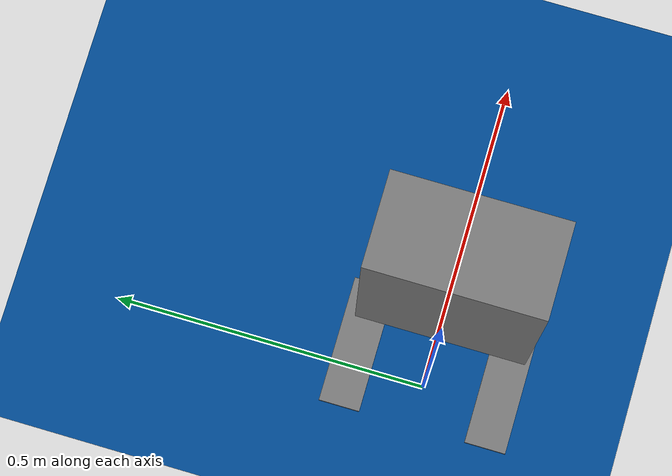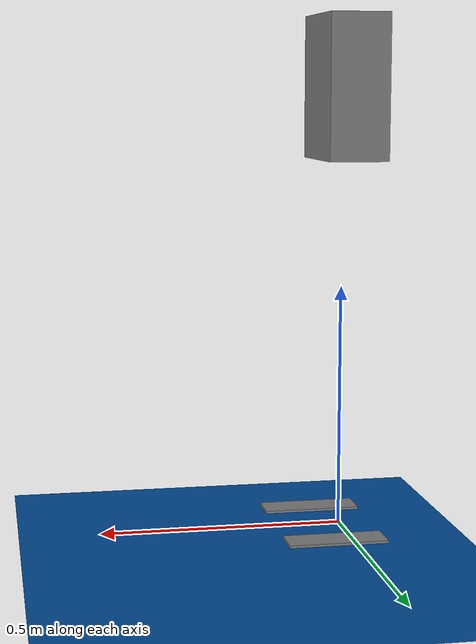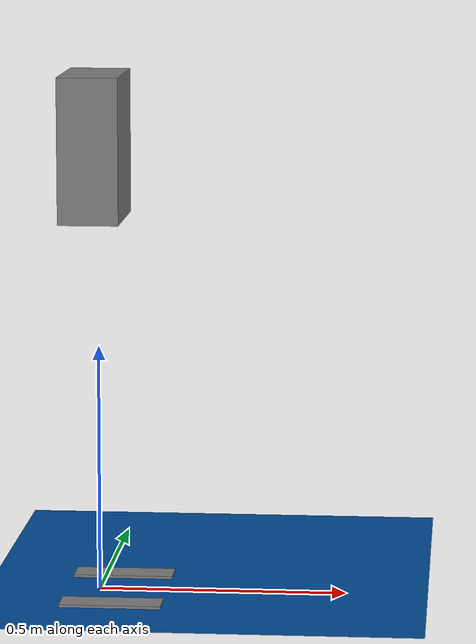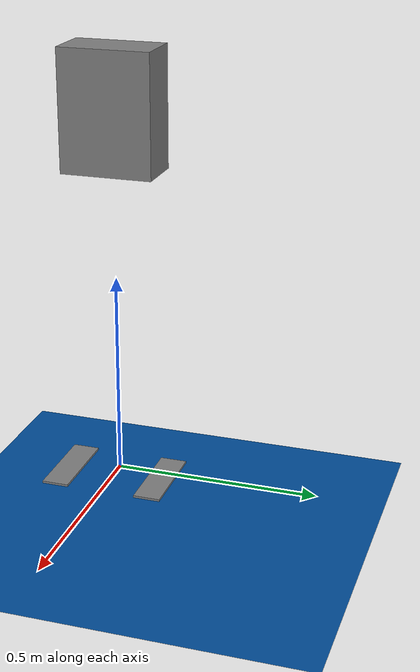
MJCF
<mujoco model="MuJoCo Model">
  <compiler angle="radian"/>

  <option tolerance="1e-06" ls_tolerance="0.01" ccd_tolerance="1e-06" sleep_tolerance="0.001" gravity="0 0 -9.81" integrator="implicitfast">
    <flag multiccd="disable"/>
  </option>

  <asset>
    <mesh name="/World/envs/env_0/Robot/left_ankle_roll_link/Cube_45" vertex="-0.101555 -0.0327346 0.00925394 0.101555 -0.0327346 0.00925394 -0.101555 0.0327346 0.00925394 0.101555 0.0327346 0.00925394 -0.101555 -0.0327346 -0.00925394 0.101555 -0.0327346 -0.00925394 -0.101555 0.0327346 -0.00925394 0.101555 0.0327346 -0.00925394" face="3 2 0 3 0 1 5 1 0 5 0 4 5 3 1 5 7 3 6 0 2 6 4 0 6 2 3 6 3 7 6 5 4 6 7 5"/>
    <mesh name="/World/envs/env_0/Robot/right_ankle_roll_link/Cube_46" vertex="-0.101555 -0.0327346 0.00925394 0.101555 -0.0327346 0.00925394 -0.101555 0.0327346 0.00925394 0.101555 0.0327346 0.00925394 -0.101555 -0.0327346 -0.00925394 0.101555 -0.0327346 -0.00925394 -0.101555 0.0327346 -0.00925394 0.101555 0.0327346 -0.00925394" face="3 2 0 3 0 1 5 1 0 5 0 4 5 3 1 5 7 3 6 0 2 6 4 0 6 2 3 6 3 7 6 5 4 6 7 5"/>
    <mesh name="/World/envs/env_0/Robot/torso_link/Cube_47" vertex="-0.06 -0.110109 0.144879 0.06 -0.110109 0.144879 -0.06 0.110109 0.144879 0.06 0.110109 0.144879 -0.06 -0.110109 -0.144879 0.06 -0.110109 -0.144879 -0.06 0.110109 -0.144879 0.06 0.110109 -0.144879" face="3 2 0 3 0 1 5 1 0 5 0 4 5 3 1 5 7 3 6 0 2 6 4 0 6 2 3 6 3 7 6 5 4 6 7 5"/>
  </asset>

  <worldbody>
    <geom name="/World/ground/terrain/GroundPlane/CollisionPlane_1" size="5 5 5" type="plane" contype="0" friction="1 0.005 0.0001" solref="0.00181818 1.375" solimp="0.9 0.95 0.001" gap="0.01" rgba="0 0.3 0.6 1"/>
    <body name="_World_envs_env_0_Robot_pelvis" pos="0 0 0.74">
      <inertial pos="0 0 -0.07605" quat="1 0 -0.000405289 0" mass="2.86" diaginertia="0.00791431 0.0069837 0.0059404"/>
      <joint name="joint_1" type="free"/>
      <body name="_World_envs_env_0_Robot_left_hip_pitch_link" pos="0 0.06445 -0.1027" quat="0.984807 0 -0.17365 0">
        <inertial pos="0.001962 0.049392 -0.000941" quat="0.420735 0.907025 -0.0155675 -0.00670647" mass="1.299" diaginertia="0.00138785 0.000955479 0.000869471"/>
        <joint name="_World_envs_env_0_Robot_pelvis_left_hip_pitch_joint" pos="0 0 0" axis="0 1 0" solimplimit="0.9 0.95 0.001" solreffriction="0.02" solimpfriction="0.9 0.95 0.001" limited="true" range="-2.35 3.05" actuatorfrclimited="true" actuatorfrcrange="-300 300" armature="0.01"/>
        <body name="_World_envs_env_0_Robot_left_hip_roll_link" pos="0 0.0523 0">
          <inertial pos="0.024757 -0.001036 -0.086323" quat="0.977498 -0.00692637 0.210181 0.0165269" mass="1.446" diaginertia="0.00244106 0.00230425 0.00142899"/>
          <joint name="_World_envs_env_0_Robot_left_hip_pitch_link_left_hip_roll_joint" pos="0 0 0" axis="1 0 0" solimplimit="0.9 0.95 0.001" solreffriction="0.02" solimpfriction="0.9 0.95 0.001" limited="true" range="-0.26 2.53" actuatorfrclimited="true" actuatorfrcrange="-300 300" armature="0.01"/>
          <body name="_World_envs_env_0_Robot_left_hip_yaw_link" pos="0.01966 -0.0012139 -0.1241">
            <inertial pos="-0.053554 -0.011477 -0.14067" quat="0.645098 0.15885 0.202109 0.71956" mass="2.052" diaginertia="0.0114476 0.0107868 0.00214501"/>
            <joint name="_World_envs_env_0_Robot_left_hip_roll_link_left_hip_yaw_joint" pos="0 0 0" axis="0 0 1" solimplimit="0.9 0.95 0.001" solreffriction="0.02" solimpfriction="0.9 0.95 0.001" limited="true" range="-2.75 2.75" actuatorfrclimited="true" actuatorfrcrange="-300 300" armature="0.01"/>
            <body name="_World_envs_env_0_Robot_left_knee_link" pos="-0.078292 -0.0017335 -0.177225" quat="0.967714 0 0.252052 0">
              <inertial pos="0.005505 0.006534 -0.116629" quat="0.799234 -0.0128893 0.0354278 0.599837" mass="2.252" diaginertia="0.0127418 0.0124382 0.00192524"/>
              <joint name="_World_envs_env_0_Robot_left_hip_yaw_link_left_knee_joint" pos="0 0 0" axis="0 1 0" solimplimit="0.9 0.95 0.001" solreffriction="0.02" solimpfriction="0.9 0.95 0.001" limited="true" range="-0.33489 2.5449" actuatorfrclimited="true" actuatorfrcrange="-300 300" armature="0.01"/>
              <body name="_World_envs_env_0_Robot_left_ankle_pitch_link" pos="0 0.0040687 -0.30007" quat="0.99678 0 -0.0801788 0">
                <inertial pos="-0.007269 0 0.011137" quat="0.603053 0.369225 0.369225 0.603053" mass="0.074" diaginertia="1.89e-05 1.40805e-05 6.9195e-06"/>
                <joint name="_World_envs_env_0_Robot_left_knee_link_left_ankle_pitch_joint" pos="0 0 0" axis="0 1 0" solimplimit="0.9 0.95 0.001" solreffriction="0.02" solimpfriction="0.9 0.95 0.001" limited="true" range="-0.68 0.73" actuatorfrclimited="true" actuatorfrcrange="-20 20" armature="0.01"/>
                <body name="_World_envs_env_0_Robot_left_ankle_roll_link" pos="0 0 -0.017558">
                  <inertial pos="0.024762 2e-05 -0.012526" quat="0.000771336 0.734476 0.000921293 0.678634" mass="0.391" diaginertia="0.00110394 0.0010657 0.000149255"/>
                  <joint name="_World_envs_env_0_Robot_left_ankle_pitch_link_left_ankle_roll_joint" pos="0 0 0" axis="1 0 0" solimplimit="0.9 0.95 0.001" solreffriction="0.02" solimpfriction="0.9 0.95 0.001" limited="true" range="-0.2618 0.2618" actuatorfrclimited="true" actuatorfrcrange="-20 20" armature="0.01"/>
                  <geom name="/World/envs/env_0/Robot/left_ankle_roll_link/Cube_45" pos="0.035917 0 -0.0251701" quat="1 0 0 0" type="mesh" conaffinity="0" friction="1 0.005 0.0001" solref="0.00181818 1.375" solimp="0.9 0.95 0.001" gap="0.01" mesh="/World/envs/env_0/Robot/left_ankle_roll_link/Cube_45"/>
                </body>
              </body>
            </body>
          </body>
        </body>
      </body>
      <body name="_World_envs_env_0_Robot_pelvis_contour_link">
        <inertial pos="0 0 0" mass="1e-06" diaginertia="1e-05 1e-05 1e-05"/>
      </body>
      <body name="_World_envs_env_0_Robot_right_hip_pitch_link" pos="0 -0.06445 -0.1027" quat="0.984807 0 -0.17365 0">
        <inertial pos="0.001962 -0.049392 -0.000941" quat="0.907025 0.420735 0.00670647 0.0155675" mass="1.299" diaginertia="0.00138785 0.000955479 0.000869471"/>
        <joint name="_World_envs_env_0_Robot_pelvis_right_hip_pitch_joint" pos="0 0 0" axis="0 1 0" solimplimit="0.9 0.95 0.001" solreffriction="0.02" solimpfriction="0.9 0.95 0.001" limited="true" range="-2.35 3.05" actuatorfrclimited="true" actuatorfrcrange="-300 300" armature="0.01"/>
        <body name="_World_envs_env_0_Robot_right_hip_roll_link" pos="0 -0.0523 0">
          <inertial pos="0.024757 0.001036 -0.086323" quat="0.977498 0.00692637 0.210181 -0.0165269" mass="1.446" diaginertia="0.00244106 0.00230425 0.00142899"/>
          <joint name="_World_envs_env_0_Robot_right_hip_pitch_link_right_hip_roll_joint" pos="0 0 0" axis="1 0 0" solimplimit="0.9 0.95 0.001" solreffriction="0.02" solimpfriction="0.9 0.95 0.001" limited="true" range="-2.53 0.26" actuatorfrclimited="true" actuatorfrcrange="-300 300" armature="0.01"/>
          <body name="_World_envs_env_0_Robot_right_hip_yaw_link" pos="0.01966 0.0012139 -0.1241">
            <inertial pos="-0.053554 0.011477 -0.14067" quat="0.71956 0.202109 0.15885 0.645098" mass="2.052" diaginertia="0.0114476 0.0107868 0.00214501"/>
            <joint name="_World_envs_env_0_Robot_right_hip_roll_link_right_hip_yaw_joint" pos="0 0 0" axis="0 0 1" solimplimit="0.9 0.95 0.001" solreffriction="0.02" solimpfriction="0.9 0.95 0.001" limited="true" range="-2.75 2.75" actuatorfrclimited="true" actuatorfrcrange="-300 300" armature="0.01"/>
            <body name="_World_envs_env_0_Robot_right_knee_link" pos="-0.078292 0.0017335 -0.177225" quat="0.967714 0 0.252052 0">
              <inertial pos="0.005505 -0.006534 -0.116629" quat="0.599837 0.0354278 -0.0128893 0.799234" mass="2.252" diaginertia="0.0127418 0.0124382 0.00192524"/>
              <joint name="_World_envs_env_0_Robot_right_hip_yaw_link_right_knee_joint" pos="0 0 0" axis="0 1 0" solimplimit="0.9 0.95 0.001" solreffriction="0.02" solimpfriction="0.9 0.95 0.001" limited="true" range="-0.33489 2.5449" actuatorfrclimited="true" actuatorfrcrange="-300 300" armature="0.01"/>
              <body name="_World_envs_env_0_Robot_right_ankle_pitch_link" pos="0 -0.0040687 -0.30007" quat="0.99678 0 -0.0801788 0">
                <inertial pos="-0.007269 0 0.011137" quat="0.603053 0.369225 0.369225 0.603053" mass="0.074" diaginertia="1.89e-05 1.40805e-05 6.9195e-06"/>
                <joint name="_World_envs_env_0_Robot_right_knee_link_right_ankle_pitch_joint" pos="0 0 0" axis="0 1 0" solimplimit="0.9 0.95 0.001" solreffriction="0.02" solimpfriction="0.9 0.95 0.001" limited="true" range="-0.68 0.73" actuatorfrclimited="true" actuatorfrcrange="-20 20" armature="0.01"/>
                <body name="_World_envs_env_0_Robot_right_ankle_roll_link" pos="0 0 -0.017558">
                  <inertial pos="0.024762 -2e-05 -0.012526" quat="-0.000771336 0.734476 -0.000921293 0.678634" mass="0.391" diaginertia="0.00110394 0.0010657 0.000149255"/>
                  <joint name="_World_envs_env_0_Robot_right_ankle_pitch_link_right_ankle_roll_joint" pos="0 0 0" axis="1 0 0" solimplimit="0.9 0.95 0.001" solreffriction="0.02" solimpfriction="0.9 0.95 0.001" limited="true" range="-0.2618 0.2618" actuatorfrclimited="true" actuatorfrcrange="-20 20" armature="0.01"/>
                  <geom name="/World/envs/env_0/Robot/right_ankle_roll_link/Cube_46" pos="0.035917 0 -0.0251701" quat="1 0 0 0" type="mesh" conaffinity="0" friction="1 0.005 0.0001" solref="0.00181818 1.375" solimp="0.9 0.95 0.001" gap="0.01" mesh="/World/envs/env_0/Robot/right_ankle_roll_link/Cube_46"/>
                </body>
              </body>
            </body>
          </body>
        </body>
      </body>
      <body name="_World_envs_env_0_Robot_torso_link">
        <inertial pos="0.00197122 0.00266902 0.169365" quat="0.999768 0.0170278 -0.0129458 -0.00253532" mass="6.3396" diaginertia="0.0603894 0.0435628 0.03337"/>
        <joint name="_World_envs_env_0_Robot_pelvis_torso_joint" pos="0 0 0" axis="0 0 1" solimplimit="0.9 0.95 0.001" solreffriction="0.02" solimpfriction="0.9 0.95 0.001" limited="true" range="-2.618 2.618" actuatorfrclimited="true" actuatorfrcrange="-300 300" armature="0.01"/>
        <geom name="/World/envs/env_0/Robot/torso_link/Cube_47" pos="-0.00620253 0 0.164763" type="mesh" conaffinity="0" friction="1 0.005 0.0001" solref="0.00181818 1.375" solimp="0.9 0.95 0.001" gap="0.01" mesh="/World/envs/env_0/Robot/torso_link/Cube_47"/>
        <body name="_World_envs_env_0_Robot_head_link">
          <inertial pos="0.00138067 0.000284309 0.420342" quat="0.721034 -0.0299186 -0.0339443 0.691421" mass="1.17977" diaginertia="0.00552903 0.00546359 0.00162239"/>
        </body>
        <body name="_World_envs_env_0_Robot_imu_link" pos="-0.0423387 0.00166 0.152067">
          <inertial pos="0 0 0" mass="1e-06" diaginertia="1e-05 1e-05 1e-05"/>
        </body>
        <body name="_World_envs_env_0_Robot_left_shoulder_pitch_link" pos="-0.0025 0.10396 0.25928" quat="0.990268 0.139172 0 0">
          <inertial pos="-0.001431 0.048811 0.001304" quat="0.786417 0.588396 -0.180543 0.0523637" mass="0.713" diaginertia="0.000466421 0.000440181 0.000410999"/>
          <joint name="_World_envs_env_0_Robot_torso_link_left_shoulder_pitch_joint" pos="0 0 0" axis="0 1 0" solimplimit="0.9 0.95 0.001" solreffriction="0.02" solimpfriction="0.9 0.95 0.001" limited="true" range="-2.9671 2.7925" actuatorfrclimited="true" actuatorfrcrange="-300 300" armature="0.01"/>
          <body name="_World_envs_env_0_Robot_left_shoulder_roll_link" pos="0 0.052 0" quat="0.990268 -0.139172 0 0">
            <inertial pos="-0.003415 0.006955 -0.064598" quat="0.70683 0.0105364 0.00575207 0.707282" mass="0.642" diaginertia="0.000683514 0.000616029 0.000372857"/>
            <joint name="_World_envs_env_0_Robot_left_shoulder_pitch_link_left_shoulder_roll_joint" pos="0 0 0" axis="1 0 0" solimplimit="0.9 0.95 0.001" solreffriction="0.02" solimpfriction="0.9 0.95 0.001" limited="true" range="-1.5882 2.2515" actuatorfrclimited="true" actuatorfrcrange="-300 300" armature="0.01"/>
            <body name="_World_envs_env_0_Robot_left_shoulder_yaw_link" pos="-0.00354 0.0062424 -0.1032">
              <inertial pos="0.000375 -0.00444 -0.072374" quat="0.903833 -0.0374183 0.00985487 0.426131" mass="0.713" diaginertia="0.000977873 0.000964661 0.000379065"/>
              <joint name="_World_envs_env_0_Robot_left_shoulder_roll_link_left_shoulder_yaw_joint" pos="0 0 0" axis="0 0 1" solimplimit="0.9 0.95 0.001" solreffriction="0.02" solimpfriction="0.9 0.95 0.001" limited="true" range="-2.618 2.618" actuatorfrclimited="true" actuatorfrcrange="-300 300" armature="0.01"/>
              <body name="_World_envs_env_0_Robot_left_elbow_pitch_link" pos="0 0.00189 -0.0855">
                <inertial pos="0.064497 0.002873 0" quat="0.582347 0.582495 0.400893 0.401069" mass="0.601" diaginertia="0.00049549 0.0004712 0.00025371"/>
                <joint name="_World_envs_env_0_Robot_left_shoulder_yaw_link_left_elbow_pitch_joint" pos="0 0 0" axis="0 1 0" solimplimit="0.9 0.95 0.001" solreffriction="0.02" solimpfriction="0.9 0.95 0.001" limited="true" range="-0.2268 3.4208" actuatorfrclimited="true" actuatorfrcrange="-300 300" armature="0.01"/>
                <body name="_World_envs_env_0_Robot_left_elbow_roll_link" pos="0.1 0 0">
                  <inertial pos="0.081811 0.001454 0.001" quat="0.459015 0.526978 0.453199 0.553363" mass="0.227" diaginertia="0.000977534 0.000968326 0.00010804"/>
                  <joint name="_World_envs_env_0_Robot_left_elbow_pitch_link_left_elbow_roll_joint" pos="0 0 0" axis="1 0 0" solimplimit="0.9 0.95 0.001" solreffriction="0.02" solimpfriction="0.9 0.95 0.001" limited="true" range="-2.0943 2.0943" actuatorfrclimited="true" actuatorfrcrange="-300 300" armature="0.01"/>
                  <body name="_World_envs_env_0_Robot_left_palm_link" pos="0.12 0 0">
                    <inertial pos="0.0557842 0.00148509 -0.000326701" quat="0.48386 0.491643 0.516022 0.507826" mass="0.28126" diaginertia="0.000311158 0.000189397 0.000176062"/>
                    <body name="_World_envs_env_0_Robot_left_five_link" pos="0.085 0.004 -0.02395">
                      <inertial pos="0.0362561 -0.0015725 0.000269899" quat="0.540443 0.459072 0.5397 0.45376" mass="0.0488469" diaginertia="8.91743e-06 8.64874e-06 3.8319e-06"/>
                      <joint name="_World_envs_env_0_Robot_left_palm_link_left_five_joint" pos="0 0 0" axis="0 0 1" solimplimit="0.9 0.95 0.001" solreffriction="0.02" solimpfriction="0.9 0.95 0.001" limited="true" range="-1.84 0.3" actuatorfrclimited="true" actuatorfrcrange="-300 300" armature="0.001"/>
                      <body name="_World_envs_env_0_Robot_left_six_link" pos="0.0471 -0.0036 0">
                        <inertial pos="0.0237591 0.00135257 0.000119669" quat="0.478926 0.48905 0.526348 0.504399" mass="0.0138583" diaginertia="2.55338e-06 2.04399e-06 9.3995e-07"/>
                        <joint name="_World_envs_env_0_Robot_left_five_link_left_six_joint" pos="0 0 0" axis="0 0 1" solimplimit="0.9 0.95 0.001" solreffriction="0.02" solimpfriction="0.9 0.95 0.001" limited="true" range="-1.84 0" actuatorfrclimited="true" actuatorfrcrange="-300 300" armature="0.001"/>
                      </body>
                    </body>
                    <body name="_World_envs_env_0_Robot_left_three_link" pos="0.085 0.004 0.02395">
                      <inertial pos="0.0362561 -0.0015725 0.000269899" quat="0.540443 0.459072 0.5397 0.45376" mass="0.0488469" diaginertia="8.91743e-06 8.64874e-06 3.8319e-06"/>
                      <joint name="_World_envs_env_0_Robot_left_palm_link_left_three_joint" pos="0 0 0" axis="0 0 1" solimplimit="0.9 0.95 0.001" solreffriction="0.02" solimpfriction="0.9 0.95 0.001" limited="true" range="-1.84 0.3" actuatorfrclimited="true" actuatorfrcrange="-300 300" armature="0.001"/>
                      <body name="_World_envs_env_0_Robot_left_four_link" pos="0.0471 -0.0036 0">
                        <inertial pos="0.0237591 0.00135257 0.000119669" quat="0.478926 0.48905 0.526348 0.504399" mass="0.0138583" diaginertia="2.55338e-06 2.04399e-06 9.3995e-07"/>
                        <joint name="_World_envs_env_0_Robot_left_three_link_left_four_joint" pos="0 0 0" axis="0 0 1" solimplimit="0.9 0.95 0.001" solreffriction="0.02" solimpfriction="0.9 0.95 0.001" limited="true" range="-1.84 0" actuatorfrclimited="true" actuatorfrcrange="-300 300" armature="0.001"/>
                      </body>
                    </body>
                    <body name="_World_envs_env_0_Robot_left_zero_link" pos="0.05 0 0">
                      <inertial pos="-0.0260466 -0.00877511 1.08605e-05" quat="0.59241 0.381376 -0.592953 0.389884" mass="0.0509893" diaginertia="8.68048e-06 7.23365e-06 4.58058e-06"/>
                      <joint name="_World_envs_env_0_Robot_left_palm_link_left_zero_joint" pos="0 0 0" axis="0 1 0" solimplimit="0.9 0.95 0.001" solreffriction="0.02" solimpfriction="0.9 0.95 0.001" limited="true" range="-0.523598 0.523598" actuatorfrclimited="true" actuatorfrcrange="-300 300" armature="0.001"/>
                      <body name="_World_envs_env_0_Robot_left_one_link" pos="-0.026525 -0.0188 -5e-05">
                        <inertial pos="-0.00181538 -0.0327057 -0.000185871" quat="0.701646 0.698199 0.081782 -0.116288" mass="0.047762" diaginertia="8.03052e-06 7.8455e-06 3.65282e-06"/>
                        <joint name="_World_envs_env_0_Robot_left_zero_link_left_one_joint" pos="0 0 0" axis="0 0 1" solimplimit="0.9 0.95 0.001" solreffriction="0.02" solimpfriction="0.9 0.95 0.001" limited="true" range="-1 1.2" actuatorfrclimited="true" actuatorfrcrange="-300 300" armature="0.001"/>
                        <body name="_World_envs_env_0_Robot_left_two_link" pos="0 -0.0431 0">
                          <inertial pos="-0.00135257 -0.0237591 -0.000119669" quat="0.717995 0.695316 -0.0180122 -0.0263741" mass="0.0138583" diaginertia="2.55338e-06 2.04399e-06 9.3995e-07"/>
                          <joint name="_World_envs_env_0_Robot_left_one_link_left_two_joint" pos="0 0 0" axis="0 0 1" solimplimit="0.9 0.95 0.001" solreffriction="0.02" solimpfriction="0.9 0.95 0.001" limited="true" range="0 1.84" actuatorfrclimited="true" actuatorfrcrange="-300 300" armature="0.001"/>
                        </body>
                      </body>
                    </body>
                  </body>
                </body>
              </body>
            </body>
          </body>
        </body>
        <body name="_World_envs_env_0_Robot_logo_link">
          <inertial pos="-0.00306556 5.62503e-05 0.245265" quat="0.00498408 0.708708 -0.00396294 0.705473" mass="0.001" diaginertia="6.88624e-06 6.44935e-06 8.95487e-07"/>
        </body>
        <body name="_World_envs_env_0_Robot_right_shoulder_pitch_link" pos="-0.0025 -0.10396 0.25928" quat="0.990268 -0.139172 0 0">
          <inertial pos="-0.001431 -0.048811 0.001304" quat="0.588396 0.786417 -0.0523637 0.180543" mass="0.713" diaginertia="0.000466421 0.000440181 0.000410999"/>
          <joint name="_World_envs_env_0_Robot_torso_link_right_shoulder_pitch_joint" pos="0 0 0" axis="0 1 0" solimplimit="0.9 0.95 0.001" solreffriction="0.02" solimpfriction="0.9 0.95 0.001" limited="true" range="-2.9671 2.7925" actuatorfrclimited="true" actuatorfrcrange="-300 300" armature="0.01"/>
          <body name="_World_envs_env_0_Robot_right_shoulder_roll_link" pos="0 -0.052 0" quat="0.990268 0.139172 0 0">
            <inertial pos="-0.003415 -0.006955 -0.064598" quat="0.707282 0.00575207 0.0105364 0.70683" mass="0.642" diaginertia="0.000683514 0.000616029 0.000372857"/>
            <joint name="_World_envs_env_0_Robot_right_shoulder_pitch_link_right_shoulder_roll_joint" pos="0 0 0" axis="1 0 0" solimplimit="0.9 0.95 0.001" solreffriction="0.02" solimpfriction="0.9 0.95 0.001" limited="true" range="-2.2515 1.5882" actuatorfrclimited="true" actuatorfrcrange="-300 300" armature="0.01"/>
            <body name="_World_envs_env_0_Robot_right_shoulder_yaw_link" pos="-0.00354 -0.0062424 -0.1032">
              <inertial pos="0.000375 0.00444 -0.072374" quat="0.426131 0.00985487 -0.0374183 0.903833" mass="0.713" diaginertia="0.000977873 0.000964661 0.000379065"/>
              <joint name="_World_envs_env_0_Robot_right_shoulder_roll_link_right_shoulder_yaw_joint" pos="0 0 0" axis="0 0 1" solimplimit="0.9 0.95 0.001" solreffriction="0.02" solimpfriction="0.9 0.95 0.001" limited="true" range="-2.618 2.618" actuatorfrclimited="true" actuatorfrcrange="-300 300" armature="0.01"/>
              <body name="_World_envs_env_0_Robot_right_elbow_pitch_link" pos="0 -0.00189 -0.0855">
                <inertial pos="0.064497 -0.002873 0" quat="0.401069 0.400893 0.582495 0.582347" mass="0.601" diaginertia="0.00049549 0.0004712 0.00025371"/>
                <joint name="_World_envs_env_0_Robot_right_shoulder_yaw_link_right_elbow_pitch_joint" pos="0 0 0" axis="0 1 0" solimplimit="0.9 0.95 0.001" solreffriction="0.02" solimpfriction="0.9 0.95 0.001" limited="true" range="-0.2268 3.4208" actuatorfrclimited="true" actuatorfrcrange="-300 300" armature="0.01"/>
                <body name="_World_envs_env_0_Robot_right_elbow_roll_link" pos="0.1 0 0">
                  <inertial pos="0.081811 -0.001454 0.001" quat="0.553363 0.453199 0.526978 0.459015" mass="0.227" diaginertia="0.000977534 0.000968326 0.00010804"/>
                  <joint name="_World_envs_env_0_Robot_right_elbow_pitch_link_right_elbow_roll_joint" pos="0 0 0" axis="1 0 0" solimplimit="0.9 0.95 0.001" solreffriction="0.02" solimpfriction="0.9 0.95 0.001" limited="true" range="-2.0943 2.0943" actuatorfrclimited="true" actuatorfrcrange="-300 300" armature="0.01"/>
                  <body name="_World_envs_env_0_Robot_right_palm_link" pos="0.12 0 0">
                    <inertial pos="0.0557842 -0.00148509 -0.000326701" quat="0.507826 0.516022 0.491643 0.48386" mass="0.28126" diaginertia="0.000311158 0.000189397 0.000176062"/>
                    <body name="_World_envs_env_0_Robot_right_five_link" pos="0.085 -0.004 -0.02395">
                      <inertial pos="0.0362561 0.0015725 0.000269899" quat="0.45376 0.5397 0.459072 0.540443" mass="0.0488469" diaginertia="8.91743e-06 8.64874e-06 3.8319e-06"/>
                      <joint name="_World_envs_env_0_Robot_right_palm_link_right_five_joint" pos="0 0 0" axis="0 0 1" solimplimit="0.9 0.95 0.001" solreffriction="0.02" solimpfriction="0.9 0.95 0.001" limited="true" range="-0.3 1.84" actuatorfrclimited="true" actuatorfrcrange="-300 300" armature="0.001"/>
                      <body name="_World_envs_env_0_Robot_right_six_link" pos="0.0471 0.0036 0">
                        <inertial pos="0.0237591 -0.00135257 0.000119669" quat="0.504399 0.526348 0.48905 0.478926" mass="0.0138583" diaginertia="2.55338e-06 2.04399e-06 9.3995e-07"/>
                        <joint name="_World_envs_env_0_Robot_right_five_link_right_six_joint" pos="0 0 0" axis="0 0 1" solimplimit="0.9 0.95 0.001" solreffriction="0.02" solimpfriction="0.9 0.95 0.001" limited="true" range="0 1.84" actuatorfrclimited="true" actuatorfrcrange="-300 300" armature="0.001"/>
                      </body>
                    </body>
                    <body name="_World_envs_env_0_Robot_right_three_link" pos="0.085 -0.004 0.02395">
                      <inertial pos="0.0362561 0.0015725 0.000269899" quat="0.45376 0.5397 0.459072 0.540443" mass="0.0488469" diaginertia="8.91743e-06 8.64874e-06 3.8319e-06"/>
                      <joint name="_World_envs_env_0_Robot_right_palm_link_right_three_joint" pos="0 0 0" axis="0 0 1" solimplimit="0.9 0.95 0.001" solreffriction="0.02" solimpfriction="0.9 0.95 0.001" limited="true" range="-0.3 1.84" actuatorfrclimited="true" actuatorfrcrange="-300 300" armature="0.001"/>
                      <body name="_World_envs_env_0_Robot_right_four_link" pos="0.0471 0.0036 0">
                        <inertial pos="0.0237591 -0.00135257 0.000119669" quat="0.504399 0.526348 0.48905 0.478926" mass="0.0138583" diaginertia="2.55338e-06 2.04399e-06 9.3995e-07"/>
                        <joint name="_World_envs_env_0_Robot_right_three_link_right_four_joint" pos="0 0 0" axis="0 0 1" solimplimit="0.9 0.95 0.001" solreffriction="0.02" solimpfriction="0.9 0.95 0.001" limited="true" range="0 1.84" actuatorfrclimited="true" actuatorfrcrange="-300 300" armature="0.001"/>
                      </body>
                    </body>
                    <body name="_World_envs_env_0_Robot_right_zero_link" pos="0.05 0 0">
                      <inertial pos="-0.0260466 0.00877511 1.08605e-05" quat="0.381376 0.59241 -0.389884 0.592953" mass="0.0509893" diaginertia="8.68048e-06 7.23365e-06 4.58058e-06"/>
                      <joint name="_World_envs_env_0_Robot_right_palm_link_right_zero_joint" pos="0 0 0" axis="0 1 0" solimplimit="0.9 0.95 0.001" solreffriction="0.02" solimpfriction="0.9 0.95 0.001" limited="true" range="-0.523598 0.523598" actuatorfrclimited="true" actuatorfrcrange="-300 300" armature="0.001"/>
                      <body name="_World_envs_env_0_Robot_right_one_link" pos="-0.026525 0.0188 -5e-05">
                        <inertial pos="-0.00181538 0.0327057 -0.000185871" quat="0.698199 0.701646 0.116288 -0.081782" mass="0.047762" diaginertia="8.03052e-06 7.8455e-06 3.65282e-06"/>
                        <joint name="_World_envs_env_0_Robot_right_zero_link_right_one_joint" pos="0 0 0" axis="0 0 1" solimplimit="0.9 0.95 0.001" solreffriction="0.02" solimpfriction="0.9 0.95 0.001" limited="true" range="-1.2 1" actuatorfrclimited="true" actuatorfrcrange="-300 300" armature="0.001"/>
                        <body name="_World_envs_env_0_Robot_right_two_link" pos="0 0.0431 0">
                          <inertial pos="-0.00135257 0.0237591 -0.000119669" quat="0.695316 0.717995 0.0263741 0.0180122" mass="0.0138583" diaginertia="2.55338e-06 2.04399e-06 9.3995e-07"/>
                          <joint name="_World_envs_env_0_Robot_right_one_link_right_two_joint" pos="0 0 0" axis="0 0 1" solimplimit="0.9 0.95 0.001" solreffriction="0.02" solimpfriction="0.9 0.95 0.001" limited="true" range="-1.84 0" actuatorfrclimited="true" actuatorfrcrange="-300 300" armature="0.001"/>
                        </body>
                      </body>
                    </body>
                  </body>
                </body>
              </body>
            </body>
          </body>
        </body>
      </body>
    </body>
  </worldbody>

  <contact>
    <exclude body1="_World_envs_env_0_Robot_pelvis" body2="_World_envs_env_0_Robot_left_hip_pitch_link"/>
    <exclude body1="_World_envs_env_0_Robot_pelvis" body2="_World_envs_env_0_Robot_left_hip_roll_link"/>
    <exclude body1="_World_envs_env_0_Robot_pelvis" body2="_World_envs_env_0_Robot_left_hip_yaw_link"/>
    <exclude body1="_World_envs_env_0_Robot_pelvis" body2="_World_envs_env_0_Robot_left_knee_link"/>
    <exclude body1="_World_envs_env_0_Robot_pelvis" body2="_World_envs_env_0_Robot_left_ankle_pitch_link"/>
    <exclude body1="_World_envs_env_0_Robot_pelvis" body2="_World_envs_env_0_Robot_left_ankle_roll_link"/>
    <exclude body1="_World_envs_env_0_Robot_pelvis" body2="_World_envs_env_0_Robot_pelvis_contour_link"/>
    <exclude body1="_World_envs_env_0_Robot_pelvis" body2="_World_envs_env_0_Robot_right_hip_pitch_link"/>
    <exclude body1="_World_envs_env_0_Robot_pelvis" body2="_World_envs_env_0_Robot_right_hip_roll_link"/>
    <exclude body1="_World_envs_env_0_Robot_pelvis" body2="_World_envs_env_0_Robot_right_hip_yaw_link"/>
    <exclude body1="_World_envs_env_0_Robot_pelvis" body2="_World_envs_env_0_Robot_right_knee_link"/>
    <exclude body1="_World_envs_env_0_Robot_pelvis" body2="_World_envs_env_0_Robot_right_ankle_pitch_link"/>
    <exclude body1="_World_envs_env_0_Robot_pelvis" body2="_World_envs_env_0_Robot_right_ankle_roll_link"/>
    <exclude body1="_World_envs_env_0_Robot_pelvis" body2="_World_envs_env_0_Robot_torso_link"/>
    <exclude body1="_World_envs_env_0_Robot_pelvis" body2="_World_envs_env_0_Robot_head_link"/>
    <exclude body1="_World_envs_env_0_Robot_pelvis" body2="_World_envs_env_0_Robot_imu_link"/>
    <exclude body1="_World_envs_env_0_Robot_pelvis" body2="_World_envs_env_0_Robot_left_shoulder_pitch_link"/>
    <exclude body1="_World_envs_env_0_Robot_pelvis" body2="_World_envs_env_0_Robot_left_shoulder_roll_link"/>
    <exclude body1="_World_envs_env_0_Robot_pelvis" body2="_World_envs_env_0_Robot_left_shoulder_yaw_link"/>
    <exclude body1="_World_envs_env_0_Robot_pelvis" body2="_World_envs_env_0_Robot_left_elbow_pitch_link"/>
    <exclude body1="_World_envs_env_0_Robot_pelvis" body2="_World_envs_env_0_Robot_left_elbow_roll_link"/>
    <exclude body1="_World_envs_env_0_Robot_pelvis" body2="_World_envs_env_0_Robot_left_palm_link"/>
    <exclude body1="_World_envs_env_0_Robot_pelvis" body2="_World_envs_env_0_Robot_left_five_link"/>
    <exclude body1="_World_envs_env_0_Robot_pelvis" body2="_World_envs_env_0_Robot_left_six_link"/>
    <exclude body1="_World_envs_env_0_Robot_pelvis" body2="_World_envs_env_0_Robot_left_three_link"/>
    <exclude body1="_World_envs_env_0_Robot_pelvis" body2="_World_envs_env_0_Robot_left_four_link"/>
    <exclude body1="_World_envs_env_0_Robot_pelvis" body2="_World_envs_env_0_Robot_left_zero_link"/>
    <exclude body1="_World_envs_env_0_Robot_pelvis" body2="_World_envs_env_0_Robot_left_one_link"/>
    <exclude body1="_World_envs_env_0_Robot_pelvis" body2="_World_envs_env_0_Robot_left_two_link"/>
    <exclude body1="_World_envs_env_0_Robot_pelvis" body2="_World_envs_env_0_Robot_logo_link"/>
    <exclude body1="_World_envs_env_0_Robot_pelvis" body2="_World_envs_env_0_Robot_right_shoulder_pitch_link"/>
    <exclude body1="_World_envs_env_0_Robot_pelvis" body2="_World_envs_env_0_Robot_right_shoulder_roll_link"/>
    <exclude body1="_World_envs_env_0_Robot_pelvis" body2="_World_envs_env_0_Robot_right_shoulder_yaw_link"/>
    <exclude body1="_World_envs_env_0_Robot_pelvis" body2="_World_envs_env_0_Robot_right_elbow_pitch_link"/>
    <exclude body1="_World_envs_env_0_Robot_pelvis" body2="_World_envs_env_0_Robot_right_elbow_roll_link"/>
    <exclude body1="_World_envs_env_0_Robot_pelvis" body2="_World_envs_env_0_Robot_right_palm_link"/>
    <exclude body1="_World_envs_env_0_Robot_pelvis" body2="_World_envs_env_0_Robot_right_five_link"/>
    <exclude body1="_World_envs_env_0_Robot_pelvis" body2="_World_envs_env_0_Robot_right_six_link"/>
    <exclude body1="_World_envs_env_0_Robot_pelvis" body2="_World_envs_env_0_Robot_right_three_link"/>
    <exclude body1="_World_envs_env_0_Robot_pelvis" body2="_World_envs_env_0_Robot_right_four_link"/>
    <exclude body1="_World_envs_env_0_Robot_pelvis" body2="_World_envs_env_0_Robot_right_zero_link"/>
    <exclude body1="_World_envs_env_0_Robot_pelvis" body2="_World_envs_env_0_Robot_right_one_link"/>
    <exclude body1="_World_envs_env_0_Robot_pelvis" body2="_World_envs_env_0_Robot_right_two_link"/>
    <exclude body1="_World_envs_env_0_Robot_left_hip_pitch_link" body2="_World_envs_env_0_Robot_left_hip_roll_link"/>
    <exclude body1="_World_envs_env_0_Robot_left_hip_pitch_link" body2="_World_envs_env_0_Robot_left_hip_yaw_link"/>
    <exclude body1="_World_envs_env_0_Robot_left_hip_pitch_link" body2="_World_envs_env_0_Robot_left_knee_link"/>
    <exclude body1="_World_envs_env_0_Robot_left_hip_pitch_link" body2="_World_envs_env_0_Robot_left_ankle_pitch_link"/>
    <exclude body1="_World_envs_env_0_Robot_left_hip_pitch_link" body2="_World_envs_env_0_Robot_left_ankle_roll_link"/>
    <exclude body1="_World_envs_env_0_Robot_left_hip_pitch_link" body2="_World_envs_env_0_Robot_pelvis_contour_link"/>
    <exclude body1="_World_envs_env_0_Robot_left_hip_pitch_link" body2="_World_envs_env_0_Robot_right_hip_pitch_link"/>
    <exclude body1="_World_envs_env_0_Robot_left_hip_pitch_link" body2="_World_envs_env_0_Robot_right_hip_roll_link"/>
    <exclude body1="_World_envs_env_0_Robot_left_hip_pitch_link" body2="_World_envs_env_0_Robot_right_hip_yaw_link"/>
    <exclude body1="_World_envs_env_0_Robot_left_hip_pitch_link" body2="_World_envs_env_0_Robot_right_knee_link"/>
    <exclude body1="_World_envs_env_0_Robot_left_hip_pitch_link" body2="_World_envs_env_0_Robot_right_ankle_pitch_link"/>
    <exclude body1="_World_envs_env_0_Robot_left_hip_pitch_link" body2="_World_envs_env_0_Robot_right_ankle_roll_link"/>
    <exclude body1="_World_envs_env_0_Robot_left_hip_pitch_link" body2="_World_envs_env_0_Robot_torso_link"/>
    <exclude body1="_World_envs_env_0_Robot_left_hip_pitch_link" body2="_World_envs_env_0_Robot_head_link"/>
    <exclude body1="_World_envs_env_0_Robot_left_hip_pitch_link" body2="_World_envs_env_0_Robot_imu_link"/>
    <exclude body1="_World_envs_env_0_Robot_left_hip_pitch_link" body2="_World_envs_env_0_Robot_left_shoulder_pitch_link"/>
    <exclude body1="_World_envs_env_0_Robot_left_hip_pitch_link" body2="_World_envs_env_0_Robot_left_shoulder_roll_link"/>
    <exclude body1="_World_envs_env_0_Robot_left_hip_pitch_link" body2="_World_envs_env_0_Robot_left_shoulder_yaw_link"/>
    <exclude body1="_World_envs_env_0_Robot_left_hip_pitch_link" body2="_World_envs_env_0_Robot_left_elbow_pitch_link"/>
    <exclude body1="_World_envs_env_0_Robot_left_hip_pitch_link" body2="_World_envs_env_0_Robot_left_elbow_roll_link"/>
    <exclude body1="_World_envs_env_0_Robot_left_hip_pitch_link" body2="_World_envs_env_0_Robot_left_palm_link"/>
    <exclude body1="_World_envs_env_0_Robot_left_hip_pitch_link" body2="_World_envs_env_0_Robot_left_five_link"/>
    <exclude body1="_World_envs_env_0_Robot_left_hip_pitch_link" body2="_World_envs_env_0_Robot_left_six_link"/>
    <exclude body1="_World_envs_env_0_Robot_left_hip_pitch_link" body2="_World_envs_env_0_Robot_left_three_link"/>
    <exclude body1="_World_envs_env_0_Robot_left_hip_pitch_link" body2="_World_envs_env_0_Robot_left_four_link"/>
    <exclude body1="_World_envs_env_0_Robot_left_hip_pitch_link" body2="_World_envs_env_0_Robot_left_zero_link"/>
    <exclude body1="_World_envs_env_0_Robot_left_hip_pitch_link" body2="_World_envs_env_0_Robot_left_one_link"/>
    <exclude body1="_World_envs_env_0_Robot_left_hip_pitch_link" body2="_World_envs_env_0_Robot_left_two_link"/>
    <exclude body1="_World_envs_env_0_Robot_left_hip_pitch_link" body2="_World_envs_env_0_Robot_logo_link"/>
    <exclude body1="_World_envs_env_0_Robot_left_hip_pitch_link" body2="_World_envs_env_0_Robot_right_shoulder_pitch_link"/>
    <exclude body1="_World_envs_env_0_Robot_left_hip_pitch_link" body2="_World_envs_env_0_Robot_right_shoulder_roll_link"/>
    <exclude body1="_World_envs_env_0_Robot_left_hip_pitch_link" body2="_World_envs_env_0_Robot_right_shoulder_yaw_link"/>
    <exclude body1="_World_envs_env_0_Robot_left_hip_pitch_link" body2="_World_envs_env_0_Robot_right_elbow_pitch_link"/>
    <exclude body1="_World_envs_env_0_Robot_left_hip_pitch_link" body2="_World_envs_env_0_Robot_right_elbow_roll_link"/>
    <exclude body1="_World_envs_env_0_Robot_left_hip_pitch_link" body2="_World_envs_env_0_Robot_right_palm_link"/>
    <exclude body1="_World_envs_env_0_Robot_left_hip_pitch_link" body2="_World_envs_env_0_Robot_right_five_link"/>
    <exclude body1="_World_envs_env_0_Robot_left_hip_pitch_link" body2="_World_envs_env_0_Robot_right_six_link"/>
    <exclude body1="_World_envs_env_0_Robot_left_hip_pitch_link" body2="_World_envs_env_0_Robot_right_three_link"/>
    <exclude body1="_World_envs_env_0_Robot_left_hip_pitch_link" body2="_World_envs_env_0_Robot_right_four_link"/>
    <exclude body1="_World_envs_env_0_Robot_left_hip_pitch_link" body2="_World_envs_env_0_Robot_right_zero_link"/>
    <exclude body1="_World_envs_env_0_Robot_left_hip_pitch_link" body2="_World_envs_env_0_Robot_right_one_link"/>
    <exclude body1="_World_envs_env_0_Robot_left_hip_pitch_link" body2="_World_envs_env_0_Robot_right_two_link"/>
    <exclude body1="_World_envs_env_0_Robot_left_hip_roll_link" body2="_World_envs_env_0_Robot_left_hip_yaw_link"/>
    <exclude body1="_World_envs_env_0_Robot_left_hip_roll_link" body2="_World_envs_env_0_Robot_left_knee_link"/>
    <exclude body1="_World_envs_env_0_Robot_left_hip_roll_link" body2="_World_envs_env_0_Robot_left_ankle_pitch_link"/>
    <exclude body1="_World_envs_env_0_Robot_left_hip_roll_link" body2="_World_envs_env_0_Robot_left_ankle_roll_link"/>
    <exclude body1="_World_envs_env_0_Robot_left_hip_roll_link" body2="_World_envs_env_0_Robot_pelvis_contour_link"/>
    <exclude body1="_World_envs_env_0_Robot_left_hip_roll_link" body2="_World_envs_env_0_Robot_right_hip_pitch_link"/>
    <exclude body1="_World_envs_env_0_Robot_left_hip_roll_link" body2="_World_envs_env_0_Robot_right_hip_roll_link"/>
    <exclude body1="_World_envs_env_0_Robot_left_hip_roll_link" body2="_World_envs_env_0_Robot_right_hip_yaw_link"/>
    <exclude body1="_World_envs_env_0_Robot_left_hip_roll_link" body2="_World_envs_env_0_Robot_right_knee_link"/>
    <exclude body1="_World_envs_env_0_Robot_left_hip_roll_link" body2="_World_envs_env_0_Robot_right_ankle_pitch_link"/>
    <exclude body1="_World_envs_env_0_Robot_left_hip_roll_link" body2="_World_envs_env_0_Robot_right_ankle_roll_link"/>
    <exclude body1="_World_envs_env_0_Robot_left_hip_roll_link" body2="_World_envs_env_0_Robot_torso_link"/>
    <exclude body1="_World_envs_env_0_Robot_left_hip_roll_link" body2="_World_envs_env_0_Robot_head_link"/>
    <exclude body1="_World_envs_env_0_Robot_left_hip_roll_link" body2="_World_envs_env_0_Robot_imu_link"/>
    <exclude body1="_World_envs_env_0_Robot_left_hip_roll_link" body2="_World_envs_env_0_Robot_left_shoulder_pitch_link"/>
    <exclude body1="_World_envs_env_0_Robot_left_hip_roll_link" body2="_World_envs_env_0_Robot_left_shoulder_roll_link"/>
    <exclude body1="_World_envs_env_0_Robot_left_hip_roll_link" body2="_World_envs_env_0_Robot_left_shoulder_yaw_link"/>
    <exclude body1="_World_envs_env_0_Robot_left_hip_roll_link" body2="_World_envs_env_0_Robot_left_elbow_pitch_link"/>
    <exclude body1="_World_envs_env_0_Robot_left_hip_roll_link" body2="_World_envs_env_0_Robot_left_elbow_roll_link"/>
    <exclude body1="_World_envs_env_0_Robot_left_hip_roll_link" body2="_World_envs_env_0_Robot_left_palm_link"/>
    <exclude body1="_World_envs_env_0_Robot_left_hip_roll_link" body2="_World_envs_env_0_Robot_left_five_link"/>
    <exclude body1="_World_envs_env_0_Robot_left_hip_roll_link" body2="_World_envs_env_0_Robot_left_six_link"/>
    <exclude body1="_World_envs_env_0_Robot_left_hip_roll_link" body2="_World_envs_env_0_Robot_left_three_link"/>
    <exclude body1="_World_envs_env_0_Robot_left_hip_roll_link" body2="_World_envs_env_0_Robot_left_four_link"/>
    <exclude body1="_World_envs_env_0_Robot_left_hip_roll_link" body2="_World_envs_env_0_Robot_left_zero_link"/>
    <exclude body1="_World_envs_env_0_Robot_left_hip_roll_link" body2="_World_envs_env_0_Robot_left_one_link"/>
    <exclude body1="_World_envs_env_0_Robot_left_hip_roll_link" body2="_World_envs_env_0_Robot_left_two_link"/>
    <exclude body1="_World_envs_env_0_Robot_left_hip_roll_link" body2="_World_envs_env_0_Robot_logo_link"/>
    <exclude body1="_World_envs_env_0_Robot_left_hip_roll_link" body2="_World_envs_env_0_Robot_right_shoulder_pitch_link"/>
    <exclude body1="_World_envs_env_0_Robot_left_hip_roll_link" body2="_World_envs_env_0_Robot_right_shoulder_roll_link"/>
    <exclude body1="_World_envs_env_0_Robot_left_hip_roll_link" body2="_World_envs_env_0_Robot_right_shoulder_yaw_link"/>
    <exclude body1="_World_envs_env_0_Robot_left_hip_roll_link" body2="_World_envs_env_0_Robot_right_elbow_pitch_link"/>
    <exclude body1="_World_envs_env_0_Robot_left_hip_roll_link" body2="_World_envs_env_0_Robot_right_elbow_roll_link"/>
    <exclude body1="_World_envs_env_0_Robot_left_hip_roll_link" body2="_World_envs_env_0_Robot_right_palm_link"/>
    <exclude body1="_World_envs_env_0_Robot_left_hip_roll_link" body2="_World_envs_env_0_Robot_right_five_link"/>
    <exclude body1="_World_envs_env_0_Robot_left_hip_roll_link" body2="_World_envs_env_0_Robot_right_six_link"/>
    <exclude body1="_World_envs_env_0_Robot_left_hip_roll_link" body2="_World_envs_env_0_Robot_right_three_link"/>
    <exclude body1="_World_envs_env_0_Robot_left_hip_roll_link" body2="_World_envs_env_0_Robot_right_four_link"/>
    <exclude body1="_World_envs_env_0_Robot_left_hip_roll_link" body2="_World_envs_env_0_Robot_right_zero_link"/>
    <exclude body1="_World_envs_env_0_Robot_left_hip_roll_link" body2="_World_envs_env_0_Robot_right_one_link"/>
    <exclude body1="_World_envs_env_0_Robot_left_hip_roll_link" body2="_World_envs_env_0_Robot_right_two_link"/>
    <exclude body1="_World_envs_env_0_Robot_left_hip_yaw_link" body2="_World_envs_env_0_Robot_left_knee_link"/>
    <exclude body1="_World_envs_env_0_Robot_left_hip_yaw_link" body2="_World_envs_env_0_Robot_left_ankle_pitch_link"/>
    <exclude body1="_World_envs_env_0_Robot_left_hip_yaw_link" body2="_World_envs_env_0_Robot_left_ankle_roll_link"/>
    <exclude body1="_World_envs_env_0_Robot_left_hip_yaw_link" body2="_World_envs_env_0_Robot_pelvis_contour_link"/>
    <exclude body1="_World_envs_env_0_Robot_left_hip_yaw_link" body2="_World_envs_env_0_Robot_right_hip_pitch_link"/>
    <exclude body1="_World_envs_env_0_Robot_left_hip_yaw_link" body2="_World_envs_env_0_Robot_right_hip_roll_link"/>
    <exclude body1="_World_envs_env_0_Robot_left_hip_yaw_link" body2="_World_envs_env_0_Robot_right_hip_yaw_link"/>
    <exclude body1="_World_envs_env_0_Robot_left_hip_yaw_link" body2="_World_envs_env_0_Robot_right_knee_link"/>
    <exclude body1="_World_envs_env_0_Robot_left_hip_yaw_link" body2="_World_envs_env_0_Robot_right_ankle_pitch_link"/>
    <exclude body1="_World_envs_env_0_Robot_left_hip_yaw_link" body2="_World_envs_env_0_Robot_right_ankle_roll_link"/>
    <exclude body1="_World_envs_env_0_Robot_left_hip_yaw_link" body2="_World_envs_env_0_Robot_torso_link"/>
    <exclude body1="_World_envs_env_0_Robot_left_hip_yaw_link" body2="_World_envs_env_0_Robot_head_link"/>
    <exclude body1="_World_envs_env_0_Robot_left_hip_yaw_link" body2="_World_envs_env_0_Robot_imu_link"/>
    <exclude body1="_World_envs_env_0_Robot_left_hip_yaw_link" body2="_World_envs_env_0_Robot_left_shoulder_pitch_link"/>
    <exclude body1="_World_envs_env_0_Robot_left_hip_yaw_link" body2="_World_envs_env_0_Robot_left_shoulder_roll_link"/>
    <exclude body1="_World_envs_env_0_Robot_left_hip_yaw_link" body2="_World_envs_env_0_Robot_left_shoulder_yaw_link"/>
    <exclude body1="_World_envs_env_0_Robot_left_hip_yaw_link" body2="_World_envs_env_0_Robot_left_elbow_pitch_link"/>
    <exclude body1="_World_envs_env_0_Robot_left_hip_yaw_link" body2="_World_envs_env_0_Robot_left_elbow_roll_link"/>
    <exclude body1="_World_envs_env_0_Robot_left_hip_yaw_link" body2="_World_envs_env_0_Robot_left_palm_link"/>
    <exclude body1="_World_envs_env_0_Robot_left_hip_yaw_link" body2="_World_envs_env_0_Robot_left_five_link"/>
    <exclude body1="_World_envs_env_0_Robot_left_hip_yaw_link" body2="_World_envs_env_0_Robot_left_six_link"/>
    <exclude body1="_World_envs_env_0_Robot_left_hip_yaw_link" body2="_World_envs_env_0_Robot_left_three_link"/>
    <exclude body1="_World_envs_env_0_Robot_left_hip_yaw_link" body2="_World_envs_env_0_Robot_left_four_link"/>
    <exclude body1="_World_envs_env_0_Robot_left_hip_yaw_link" body2="_World_envs_env_0_Robot_left_zero_link"/>
    <exclude body1="_World_envs_env_0_Robot_left_hip_yaw_link" body2="_World_envs_env_0_Robot_left_one_link"/>
    <exclude body1="_World_envs_env_0_Robot_left_hip_yaw_link" body2="_World_envs_env_0_Robot_left_two_link"/>
    <exclude body1="_World_envs_env_0_Robot_left_hip_yaw_link" body2="_World_envs_env_0_Robot_logo_link"/>
    <exclude body1="_World_envs_env_0_Robot_left_hip_yaw_link" body2="_World_envs_env_0_Robot_right_shoulder_pitch_link"/>
    <exclude body1="_World_envs_env_0_Robot_left_hip_yaw_link" body2="_World_envs_env_0_Robot_right_shoulder_roll_link"/>
    <exclude body1="_World_envs_env_0_Robot_left_hip_yaw_link" body2="_World_envs_env_0_Robot_right_shoulder_yaw_link"/>
    <exclude body1="_World_envs_env_0_Robot_left_hip_yaw_link" body2="_World_envs_env_0_Robot_right_elbow_pitch_link"/>
    <exclude body1="_World_envs_env_0_Robot_left_hip_yaw_link" body2="_World_envs_env_0_Robot_right_elbow_roll_link"/>
    <exclude body1="_World_envs_env_0_Robot_left_hip_yaw_link" body2="_World_envs_env_0_Robot_right_palm_link"/>
    <exclude body1="_World_envs_env_0_Robot_left_hip_yaw_link" body2="_World_envs_env_0_Robot_right_five_link"/>
    <exclude body1="_World_envs_env_0_Robot_left_hip_yaw_link" body2="_World_envs_env_0_Robot_right_six_link"/>
    <exclude body1="_World_envs_env_0_Robot_left_hip_yaw_link" body2="_World_envs_env_0_Robot_right_three_link"/>
    <exclude body1="_World_envs_env_0_Robot_left_hip_yaw_link" body2="_World_envs_env_0_Robot_right_four_link"/>
    <exclude body1="_World_envs_env_0_Robot_left_hip_yaw_link" body2="_World_envs_env_0_Robot_right_zero_link"/>
    <exclude body1="_World_envs_env_0_Robot_left_hip_yaw_link" body2="_World_envs_env_0_Robot_right_one_link"/>
    <exclude body1="_World_envs_env_0_Robot_left_hip_yaw_link" body2="_World_envs_env_0_Robot_right_two_link"/>
    <exclude body1="_World_envs_env_0_Robot_left_knee_link" body2="_World_envs_env_0_Robot_left_ankle_pitch_link"/>
    <exclude body1="_World_envs_env_0_Robot_left_knee_link" body2="_World_envs_env_0_Robot_left_ankle_roll_link"/>
    <exclude body1="_World_envs_env_0_Robot_left_knee_link" body2="_World_envs_env_0_Robot_pelvis_contour_link"/>
    <exclude body1="_World_envs_env_0_Robot_left_knee_link" body2="_World_envs_env_0_Robot_right_hip_pitch_link"/>
    <exclude body1="_World_envs_env_0_Robot_left_knee_link" body2="_World_envs_env_0_Robot_right_hip_roll_link"/>
    <exclude body1="_World_envs_env_0_Robot_left_knee_link" body2="_World_envs_env_0_Robot_right_hip_yaw_link"/>
    <exclude body1="_World_envs_env_0_Robot_left_knee_link" body2="_World_envs_env_0_Robot_right_knee_link"/>
    <exclude body1="_World_envs_env_0_Robot_left_knee_link" body2="_World_envs_env_0_Robot_right_ankle_pitch_link"/>
    <exclude body1="_World_envs_env_0_Robot_left_knee_link" body2="_World_envs_env_0_Robot_right_ankle_roll_link"/>
    <exclude body1="_World_envs_env_0_Robot_left_knee_link" body2="_World_envs_env_0_Robot_torso_link"/>
    <exclude body1="_World_envs_env_0_Robot_left_knee_link" body2="_World_envs_env_0_Robot_head_link"/>
    <exclude body1="_World_envs_env_0_Robot_left_knee_link" body2="_World_envs_env_0_Robot_imu_link"/>
    <exclude body1="_World_envs_env_0_Robot_left_knee_link" body2="_World_envs_env_0_Robot_left_shoulder_pitch_link"/>
    <exclude body1="_World_envs_env_0_Robot_left_knee_link" body2="_World_envs_env_0_Robot_left_shoulder_roll_link"/>
    <exclude body1="_World_envs_env_0_Robot_left_knee_link" body2="_World_envs_env_0_Robot_left_shoulder_yaw_link"/>
    <exclude body1="_World_envs_env_0_Robot_left_knee_link" body2="_World_envs_env_0_Robot_left_elbow_pitch_link"/>
    <exclude body1="_World_envs_env_0_Robot_left_knee_link" body2="_World_envs_env_0_Robot_left_elbow_roll_link"/>
    <exclude body1="_World_envs_env_0_Robot_left_knee_link" body2="_World_envs_env_0_Robot_left_palm_link"/>
    <exclude body1="_World_envs_env_0_Robot_left_knee_link" body2="_World_envs_env_0_Robot_left_five_link"/>
    <exclude body1="_World_envs_env_0_Robot_left_knee_link" body2="_World_envs_env_0_Robot_left_six_link"/>
    <exclude body1="_World_envs_env_0_Robot_left_knee_link" body2="_World_envs_env_0_Robot_left_three_link"/>
    <exclude body1="_World_envs_env_0_Robot_left_knee_link" body2="_World_envs_env_0_Robot_left_four_link"/>
    <exclude body1="_World_envs_env_0_Robot_left_knee_link" body2="_World_envs_env_0_Robot_left_zero_link"/>
    <exclude body1="_World_envs_env_0_Robot_left_knee_link" body2="_World_envs_env_0_Robot_left_one_link"/>
    <exclude body1="_World_envs_env_0_Robot_left_knee_link" body2="_World_envs_env_0_Robot_left_two_link"/>
    <exclude body1="_World_envs_env_0_Robot_left_knee_link" body2="_World_envs_env_0_Robot_logo_link"/>
    <exclude body1="_World_envs_env_0_Robot_left_knee_link" body2="_World_envs_env_0_Robot_right_shoulder_pitch_link"/>
    <exclude body1="_World_envs_env_0_Robot_left_knee_link" body2="_World_envs_env_0_Robot_right_shoulder_roll_link"/>
    <exclude body1="_World_envs_env_0_Robot_left_knee_link" body2="_World_envs_env_0_Robot_right_shoulder_yaw_link"/>
    <exclude body1="_World_envs_env_0_Robot_left_knee_link" body2="_World_envs_env_0_Robot_right_elbow_pitch_link"/>
    <exclude body1="_World_envs_env_0_Robot_left_knee_link" body2="_World_envs_env_0_Robot_right_elbow_roll_link"/>
    <exclude body1="_World_envs_env_0_Robot_left_knee_link" body2="_World_envs_env_0_Robot_right_palm_link"/>
    <exclude body1="_World_envs_env_0_Robot_left_knee_link" body2="_World_envs_env_0_Robot_right_five_link"/>
    <exclude body1="_World_envs_env_0_Robot_left_knee_link" body2="_World_envs_env_0_Robot_right_six_link"/>
    <exclude body1="_World_envs_env_0_Robot_left_knee_link" body2="_World_envs_env_0_Robot_right_three_link"/>
    <exclude body1="_World_envs_env_0_Robot_left_knee_link" body2="_World_envs_env_0_Robot_right_four_link"/>
    <exclude body1="_World_envs_env_0_Robot_left_knee_link" body2="_World_envs_env_0_Robot_right_zero_link"/>
    <exclude body1="_World_envs_env_0_Robot_left_knee_link" body2="_World_envs_env_0_Robot_right_one_link"/>
    <exclude body1="_World_envs_env_0_Robot_left_knee_link" body2="_World_envs_env_0_Robot_right_two_link"/>
    <exclude body1="_World_envs_env_0_Robot_left_ankle_pitch_link" body2="_World_envs_env_0_Robot_left_ankle_roll_link"/>
    <exclude body1="_World_envs_env_0_Robot_left_ankle_pitch_link" body2="_World_envs_env_0_Robot_pelvis_contour_link"/>
    <exclude body1="_World_envs_env_0_Robot_left_ankle_pitch_link" body2="_World_envs_env_0_Robot_right_hip_pitch_link"/>
    <exclude body1="_World_envs_env_0_Robot_left_ankle_pitch_link" body2="_World_envs_env_0_Robot_right_hip_roll_link"/>
    <exclude body1="_World_envs_env_0_Robot_left_ankle_pitch_link" body2="_World_envs_env_0_Robot_right_hip_yaw_link"/>
    <exclude body1="_World_envs_env_0_Robot_left_ankle_pitch_link" body2="_World_envs_env_0_Robot_right_knee_link"/>
    <exclude body1="_World_envs_env_0_Robot_left_ankle_pitch_link" body2="_World_envs_env_0_Robot_right_ankle_pitch_link"/>
    <exclude body1="_World_envs_env_0_Robot_left_ankle_pitch_link" body2="_World_envs_env_0_Robot_right_ankle_roll_link"/>
    <exclude body1="_World_envs_env_0_Robot_left_ankle_pitch_link" body2="_World_envs_env_0_Robot_torso_link"/>
    <exclude body1="_World_envs_env_0_Robot_left_ankle_pitch_link" body2="_World_envs_env_0_Robot_head_link"/>
    <exclude body1="_World_envs_env_0_Robot_left_ankle_pitch_link" body2="_World_envs_env_0_Robot_imu_link"/>
    <exclude body1="_World_envs_env_0_Robot_left_ankle_pitch_link" body2="_World_envs_env_0_Robot_left_shoulder_pitch_link"/>
    <exclude body1="_World_envs_env_0_Robot_left_ankle_pitch_link" body2="_World_envs_env_0_Robot_left_shoulder_roll_link"/>
    <exclude body1="_World_envs_env_0_Robot_left_ankle_pitch_link" body2="_World_envs_env_0_Robot_left_shoulder_yaw_link"/>
    <exclude body1="_World_envs_env_0_Robot_left_ankle_pitch_link" body2="_World_envs_env_0_Robot_left_elbow_pitch_link"/>
    <exclude body1="_World_envs_env_0_Robot_left_ankle_pitch_link" body2="_World_envs_env_0_Robot_left_elbow_roll_link"/>
    <exclude body1="_World_envs_env_0_Robot_left_ankle_pitch_link" body2="_World_envs_env_0_Robot_left_palm_link"/>
    <exclude body1="_World_envs_env_0_Robot_left_ankle_pitch_link" body2="_World_envs_env_0_Robot_left_five_link"/>
    <exclude body1="_World_envs_env_0_Robot_left_ankle_pitch_link" body2="_World_envs_env_0_Robot_left_six_link"/>
    <exclude body1="_World_envs_env_0_Robot_left_ankle_pitch_link" body2="_World_envs_env_0_Robot_left_three_link"/>
    <exclude body1="_World_envs_env_0_Robot_left_ankle_pitch_link" body2="_World_envs_env_0_Robot_left_four_link"/>
    <exclude body1="_World_envs_env_0_Robot_left_ankle_pitch_link" body2="_World_envs_env_0_Robot_left_zero_link"/>
    <exclude body1="_World_envs_env_0_Robot_left_ankle_pitch_link" body2="_World_envs_env_0_Robot_left_one_link"/>
    <exclude body1="_World_envs_env_0_Robot_left_ankle_pitch_link" body2="_World_envs_env_0_Robot_left_two_link"/>
    <exclude body1="_World_envs_env_0_Robot_left_ankle_pitch_link" body2="_World_envs_env_0_Robot_logo_link"/>
    <exclude body1="_World_envs_env_0_Robot_left_ankle_pitch_link" body2="_World_envs_env_0_Robot_right_shoulder_pitch_link"/>
    <exclude body1="_World_envs_env_0_Robot_left_ankle_pitch_link" body2="_World_envs_env_0_Robot_right_shoulder_roll_link"/>
    <exclude body1="_World_envs_env_0_Robot_left_ankle_pitch_link" body2="_World_envs_env_0_Robot_right_shoulder_yaw_link"/>
    <exclude body1="_World_envs_env_0_Robot_left_ankle_pitch_link" body2="_World_envs_env_0_Robot_right_elbow_pitch_link"/>
    <exclude body1="_World_envs_env_0_Robot_left_ankle_pitch_link" body2="_World_envs_env_0_Robot_right_elbow_roll_link"/>
    <exclude body1="_World_envs_env_0_Robot_left_ankle_pitch_link" body2="_World_envs_env_0_Robot_right_palm_link"/>
    <exclude body1="_World_envs_env_0_Robot_left_ankle_pitch_link" body2="_World_envs_env_0_Robot_right_five_link"/>
    <exclude body1="_World_envs_env_0_Robot_left_ankle_pitch_link" body2="_World_envs_env_0_Robot_right_six_link"/>
    <exclude body1="_World_envs_env_0_Robot_left_ankle_pitch_link" body2="_World_envs_env_0_Robot_right_three_link"/>
    <exclude body1="_World_envs_env_0_Robot_left_ankle_pitch_link" body2="_World_envs_env_0_Robot_right_four_link"/>
    <exclude body1="_World_envs_env_0_Robot_left_ankle_pitch_link" body2="_World_envs_env_0_Robot_right_zero_link"/>
    <exclude body1="_World_envs_env_0_Robot_left_ankle_pitch_link" body2="_World_envs_env_0_Robot_right_one_link"/>
    <exclude body1="_World_envs_env_0_Robot_left_ankle_pitch_link" body2="_World_envs_env_0_Robot_right_two_link"/>
    <exclude body1="_World_envs_env_0_Robot_left_ankle_roll_link" body2="_World_envs_env_0_Robot_pelvis_contour_link"/>
    <exclude body1="_World_envs_env_0_Robot_left_ankle_roll_link" body2="_World_envs_env_0_Robot_right_hip_pitch_link"/>
    <exclude body1="_World_envs_env_0_Robot_left_ankle_roll_link" body2="_World_envs_env_0_Robot_right_hip_roll_link"/>
    <exclude body1="_World_envs_env_0_Robot_left_ankle_roll_link" body2="_World_envs_env_0_Robot_right_hip_yaw_link"/>
    <exclude body1="_World_envs_env_0_Robot_left_ankle_roll_link" body2="_World_envs_env_0_Robot_right_knee_link"/>
    <exclude body1="_World_envs_env_0_Robot_left_ankle_roll_link" body2="_World_envs_env_0_Robot_right_ankle_pitch_link"/>
    <exclude body1="_World_envs_env_0_Robot_left_ankle_roll_link" body2="_World_envs_env_0_Robot_right_ankle_roll_link"/>
    <exclude body1="_World_envs_env_0_Robot_left_ankle_roll_link" body2="_World_envs_env_0_Robot_torso_link"/>
    <exclude body1="_World_envs_env_0_Robot_left_ankle_roll_link" body2="_World_envs_env_0_Robot_head_link"/>
    <exclude body1="_World_envs_env_0_Robot_left_ankle_roll_link" body2="_World_envs_env_0_Robot_imu_link"/>
    <exclude body1="_World_envs_env_0_Robot_left_ankle_roll_link" body2="_World_envs_env_0_Robot_left_shoulder_pitch_link"/>
    <exclude body1="_World_envs_env_0_Robot_left_ankle_roll_link" body2="_World_envs_env_0_Robot_left_shoulder_roll_link"/>
    <exclude body1="_World_envs_env_0_Robot_left_ankle_roll_link" body2="_World_envs_env_0_Robot_left_shoulder_yaw_link"/>
    <exclude body1="_World_envs_env_0_Robot_left_ankle_roll_link" body2="_World_envs_env_0_Robot_left_elbow_pitch_link"/>
    <exclude body1="_World_envs_env_0_Robot_left_ankle_roll_link" body2="_World_envs_env_0_Robot_left_elbow_roll_link"/>
    <exclude body1="_World_envs_env_0_Robot_left_ankle_roll_link" body2="_World_envs_env_0_Robot_left_palm_link"/>
    <exclude body1="_World_envs_env_0_Robot_left_ankle_roll_link" body2="_World_envs_env_0_Robot_left_five_link"/>
    <exclude body1="_World_envs_env_0_Robot_left_ankle_roll_link" body2="_World_envs_env_0_Robot_left_six_link"/>
    <exclude body1="_World_envs_env_0_Robot_left_ankle_roll_link" body2="_World_envs_env_0_Robot_left_three_link"/>
    <exclude body1="_World_envs_env_0_Robot_left_ankle_roll_link" body2="_World_envs_env_0_Robot_left_four_link"/>
    <exclude body1="_World_envs_env_0_Robot_left_ankle_roll_link" body2="_World_envs_env_0_Robot_left_zero_link"/>
    <exclude body1="_World_envs_env_0_Robot_left_ankle_roll_link" body2="_World_envs_env_0_Robot_left_one_link"/>
    <exclude body1="_World_envs_env_0_Robot_left_ankle_roll_link" body2="_World_envs_env_0_Robot_left_two_link"/>
    <exclude body1="_World_envs_env_0_Robot_left_ankle_roll_link" body2="_World_envs_env_0_Robot_logo_link"/>
    <exclude body1="_World_envs_env_0_Robot_left_ankle_roll_link" body2="_World_envs_env_0_Robot_right_shoulder_pitch_link"/>
    <exclude body1="_World_envs_env_0_Robot_left_ankle_roll_link" body2="_World_envs_env_0_Robot_right_shoulder_roll_link"/>
    <exclude body1="_World_envs_env_0_Robot_left_ankle_roll_link" body2="_World_envs_env_0_Robot_right_shoulder_yaw_link"/>
    <exclude body1="_World_envs_env_0_Robot_left_ankle_roll_link" body2="_World_envs_env_0_Robot_right_elbow_pitch_link"/>
    <exclude body1="_World_envs_env_0_Robot_left_ankle_roll_link" body2="_World_envs_env_0_Robot_right_elbow_roll_link"/>
    <exclude body1="_World_envs_env_0_Robot_left_ankle_roll_link" body2="_World_envs_env_0_Robot_right_palm_link"/>
    <exclude body1="_World_envs_env_0_Robot_left_ankle_roll_link" body2="_World_envs_env_0_Robot_right_five_link"/>
    <exclude body1="_World_envs_env_0_Robot_left_ankle_roll_link" body2="_World_envs_env_0_Robot_right_six_link"/>
    <exclude body1="_World_envs_env_0_Robot_left_ankle_roll_link" body2="_World_envs_env_0_Robot_right_three_link"/>
    <exclude body1="_World_envs_env_0_Robot_left_ankle_roll_link" body2="_World_envs_env_0_Robot_right_four_link"/>
    <exclude body1="_World_envs_env_0_Robot_left_ankle_roll_link" body2="_World_envs_env_0_Robot_right_zero_link"/>
    <exclude body1="_World_envs_env_0_Robot_left_ankle_roll_link" body2="_World_envs_env_0_Robot_right_one_link"/>
    <exclude body1="_World_envs_env_0_Robot_left_ankle_roll_link" body2="_World_envs_env_0_Robot_right_two_link"/>
    <exclude body1="_World_envs_env_0_Robot_pelvis_contour_link" body2="_World_envs_env_0_Robot_right_hip_pitch_link"/>
    <exclude body1="_World_envs_env_0_Robot_pelvis_contour_link" body2="_World_envs_env_0_Robot_right_hip_roll_link"/>
    <exclude body1="_World_envs_env_0_Robot_pelvis_contour_link" body2="_World_envs_env_0_Robot_right_hip_yaw_link"/>
    <exclude body1="_World_envs_env_0_Robot_pelvis_contour_link" body2="_World_envs_env_0_Robot_right_knee_link"/>
    <exclude body1="_World_envs_env_0_Robot_pelvis_contour_link" body2="_World_envs_env_0_Robot_right_ankle_pitch_link"/>
    <exclude body1="_World_envs_env_0_Robot_pelvis_contour_link" body2="_World_envs_env_0_Robot_right_ankle_roll_link"/>
    <exclude body1="_World_envs_env_0_Robot_pelvis_contour_link" body2="_World_envs_env_0_Robot_torso_link"/>
    <exclude body1="_World_envs_env_0_Robot_pelvis_contour_link" body2="_World_envs_env_0_Robot_head_link"/>
    <exclude body1="_World_envs_env_0_Robot_pelvis_contour_link" body2="_World_envs_env_0_Robot_imu_link"/>
    <exclude body1="_World_envs_env_0_Robot_pelvis_contour_link" body2="_World_envs_env_0_Robot_left_shoulder_pitch_link"/>
    <exclude body1="_World_envs_env_0_Robot_pelvis_contour_link" body2="_World_envs_env_0_Robot_left_shoulder_roll_link"/>
    <exclude body1="_World_envs_env_0_Robot_pelvis_contour_link" body2="_World_envs_env_0_Robot_left_shoulder_yaw_link"/>
    <exclude body1="_World_envs_env_0_Robot_pelvis_contour_link" body2="_World_envs_env_0_Robot_left_elbow_pitch_link"/>
    <exclude body1="_World_envs_env_0_Robot_pelvis_contour_link" body2="_World_envs_env_0_Robot_left_elbow_roll_link"/>
    <exclude body1="_World_envs_env_0_Robot_pelvis_contour_link" body2="_World_envs_env_0_Robot_left_palm_link"/>
    <exclude body1="_World_envs_env_0_Robot_pelvis_contour_link" body2="_World_envs_env_0_Robot_left_five_link"/>
    <exclude body1="_World_envs_env_0_Robot_pelvis_contour_link" body2="_World_envs_env_0_Robot_left_six_link"/>
    <exclude body1="_World_envs_env_0_Robot_pelvis_contour_link" body2="_World_envs_env_0_Robot_left_three_link"/>
    <exclude body1="_World_envs_env_0_Robot_pelvis_contour_link" body2="_World_envs_env_0_Robot_left_four_link"/>
    <exclude body1="_World_envs_env_0_Robot_pelvis_contour_link" body2="_World_envs_env_0_Robot_left_zero_link"/>
    <exclude body1="_World_envs_env_0_Robot_pelvis_contour_link" body2="_World_envs_env_0_Robot_left_one_link"/>
    <exclude body1="_World_envs_env_0_Robot_pelvis_contour_link" body2="_World_envs_env_0_Robot_left_two_link"/>
    <exclude body1="_World_envs_env_0_Robot_pelvis_contour_link" body2="_World_envs_env_0_Robot_logo_link"/>
    <exclude body1="_World_envs_env_0_Robot_pelvis_contour_link" body2="_World_envs_env_0_Robot_right_shoulder_pitch_link"/>
    <exclude body1="_World_envs_env_0_Robot_pelvis_contour_link" body2="_World_envs_env_0_Robot_right_shoulder_roll_link"/>
    <exclude body1="_World_envs_env_0_Robot_pelvis_contour_link" body2="_World_envs_env_0_Robot_right_shoulder_yaw_link"/>
    <exclude body1="_World_envs_env_0_Robot_pelvis_contour_link" body2="_World_envs_env_0_Robot_right_elbow_pitch_link"/>
    <exclude body1="_World_envs_env_0_Robot_pelvis_contour_link" body2="_World_envs_env_0_Robot_right_elbow_roll_link"/>
    <exclude body1="_World_envs_env_0_Robot_pelvis_contour_link" body2="_World_envs_env_0_Robot_right_palm_link"/>
    <exclude body1="_World_envs_env_0_Robot_pelvis_contour_link" body2="_World_envs_env_0_Robot_right_five_link"/>
    <exclude body1="_World_envs_env_0_Robot_pelvis_contour_link" body2="_World_envs_env_0_Robot_right_six_link"/>
    <exclude body1="_World_envs_env_0_Robot_pelvis_contour_link" body2="_World_envs_env_0_Robot_right_three_link"/>
    <exclude body1="_World_envs_env_0_Robot_pelvis_contour_link" body2="_World_envs_env_0_Robot_right_four_link"/>
    <exclude body1="_World_envs_env_0_Robot_pelvis_contour_link" body2="_World_envs_env_0_Robot_right_zero_link"/>
    <exclude body1="_World_envs_env_0_Robot_pelvis_contour_link" body2="_World_envs_env_0_Robot_right_one_link"/>
    <exclude body1="_World_envs_env_0_Robot_pelvis_contour_link" body2="_World_envs_env_0_Robot_right_two_link"/>
    <exclude body1="_World_envs_env_0_Robot_right_hip_pitch_link" body2="_World_envs_env_0_Robot_right_hip_roll_link"/>
    <exclude body1="_World_envs_env_0_Robot_right_hip_pitch_link" body2="_World_envs_env_0_Robot_right_hip_yaw_link"/>
    <exclude body1="_World_envs_env_0_Robot_right_hip_pitch_link" body2="_World_envs_env_0_Robot_right_knee_link"/>
    <exclude body1="_World_envs_env_0_Robot_right_hip_pitch_link" body2="_World_envs_env_0_Robot_right_ankle_pitch_link"/>
    <exclude body1="_World_envs_env_0_Robot_right_hip_pitch_link" body2="_World_envs_env_0_Robot_right_ankle_roll_link"/>
    <exclude body1="_World_envs_env_0_Robot_right_hip_pitch_link" body2="_World_envs_env_0_Robot_torso_link"/>
    <exclude body1="_World_envs_env_0_Robot_right_hip_pitch_link" body2="_World_envs_env_0_Robot_head_link"/>
    <exclude body1="_World_envs_env_0_Robot_right_hip_pitch_link" body2="_World_envs_env_0_Robot_imu_link"/>
    <exclude body1="_World_envs_env_0_Robot_right_hip_pitch_link" body2="_World_envs_env_0_Robot_left_shoulder_pitch_link"/>
    <exclude body1="_World_envs_env_0_Robot_right_hip_pitch_link" body2="_World_envs_env_0_Robot_left_shoulder_roll_link"/>
    <exclude body1="_World_envs_env_0_Robot_right_hip_pitch_link" body2="_World_envs_env_0_Robot_left_shoulder_yaw_link"/>
    <exclude body1="_World_envs_env_0_Robot_right_hip_pitch_link" body2="_World_envs_env_0_Robot_left_elbow_pitch_link"/>
    <exclude body1="_World_envs_env_0_Robot_right_hip_pitch_link" body2="_World_envs_env_0_Robot_left_elbow_roll_link"/>
    <exclude body1="_World_envs_env_0_Robot_right_hip_pitch_link" body2="_World_envs_env_0_Robot_left_palm_link"/>
    <exclude body1="_World_envs_env_0_Robot_right_hip_pitch_link" body2="_World_envs_env_0_Robot_left_five_link"/>
    <exclude body1="_World_envs_env_0_Robot_right_hip_pitch_link" body2="_World_envs_env_0_Robot_left_six_link"/>
    <exclude body1="_World_envs_env_0_Robot_right_hip_pitch_link" body2="_World_envs_env_0_Robot_left_three_link"/>
    <exclude body1="_World_envs_env_0_Robot_right_hip_pitch_link" body2="_World_envs_env_0_Robot_left_four_link"/>
    <exclude body1="_World_envs_env_0_Robot_right_hip_pitch_link" body2="_World_envs_env_0_Robot_left_zero_link"/>
    <exclude body1="_World_envs_env_0_Robot_right_hip_pitch_link" body2="_World_envs_env_0_Robot_left_one_link"/>
    <exclude body1="_World_envs_env_0_Robot_right_hip_pitch_link" body2="_World_envs_env_0_Robot_left_two_link"/>
    <exclude body1="_World_envs_env_0_Robot_right_hip_pitch_link" body2="_World_envs_env_0_Robot_logo_link"/>
    <exclude body1="_World_envs_env_0_Robot_right_hip_pitch_link" body2="_World_envs_env_0_Robot_right_shoulder_pitch_link"/>
    <exclude body1="_World_envs_env_0_Robot_right_hip_pitch_link" body2="_World_envs_env_0_Robot_right_shoulder_roll_link"/>
    <exclude body1="_World_envs_env_0_Robot_right_hip_pitch_link" body2="_World_envs_env_0_Robot_right_shoulder_yaw_link"/>
    <exclude body1="_World_envs_env_0_Robot_right_hip_pitch_link" body2="_World_envs_env_0_Robot_right_elbow_pitch_link"/>
    <exclude body1="_World_envs_env_0_Robot_right_hip_pitch_link" body2="_World_envs_env_0_Robot_right_elbow_roll_link"/>
    <exclude body1="_World_envs_env_0_Robot_right_hip_pitch_link" body2="_World_envs_env_0_Robot_right_palm_link"/>
    <exclude body1="_World_envs_env_0_Robot_right_hip_pitch_link" body2="_World_envs_env_0_Robot_right_five_link"/>
    <exclude body1="_World_envs_env_0_Robot_right_hip_pitch_link" body2="_World_envs_env_0_Robot_right_six_link"/>
    <exclude body1="_World_envs_env_0_Robot_right_hip_pitch_link" body2="_World_envs_env_0_Robot_right_three_link"/>
    <exclude body1="_World_envs_env_0_Robot_right_hip_pitch_link" body2="_World_envs_env_0_Robot_right_four_link"/>
    <exclude body1="_World_envs_env_0_Robot_right_hip_pitch_link" body2="_World_envs_env_0_Robot_right_zero_link"/>
    <exclude body1="_World_envs_env_0_Robot_right_hip_pitch_link" body2="_World_envs_env_0_Robot_right_one_link"/>
    <exclude body1="_World_envs_env_0_Robot_right_hip_pitch_link" body2="_World_envs_env_0_Robot_right_two_link"/>
    <exclude body1="_World_envs_env_0_Robot_right_hip_roll_link" body2="_World_envs_env_0_Robot_right_hip_yaw_link"/>
    <exclude body1="_World_envs_env_0_Robot_right_hip_roll_link" body2="_World_envs_env_0_Robot_right_knee_link"/>
    <exclude body1="_World_envs_env_0_Robot_right_hip_roll_link" body2="_World_envs_env_0_Robot_right_ankle_pitch_link"/>
    <exclude body1="_World_envs_env_0_Robot_right_hip_roll_link" body2="_World_envs_env_0_Robot_right_ankle_roll_link"/>
    <exclude body1="_World_envs_env_0_Robot_right_hip_roll_link" body2="_World_envs_env_0_Robot_torso_link"/>
    <exclude body1="_World_envs_env_0_Robot_right_hip_roll_link" body2="_World_envs_env_0_Robot_head_link"/>
    <exclude body1="_World_envs_env_0_Robot_right_hip_roll_link" body2="_World_envs_env_0_Robot_imu_link"/>
    <exclude body1="_World_envs_env_0_Robot_right_hip_roll_link" body2="_World_envs_env_0_Robot_left_shoulder_pitch_link"/>
    <exclude body1="_World_envs_env_0_Robot_right_hip_roll_link" body2="_World_envs_env_0_Robot_left_shoulder_roll_link"/>
    <exclude body1="_World_envs_env_0_Robot_right_hip_roll_link" body2="_World_envs_env_0_Robot_left_shoulder_yaw_link"/>
    <exclude body1="_World_envs_env_0_Robot_right_hip_roll_link" body2="_World_envs_env_0_Robot_left_elbow_pitch_link"/>
    <exclude body1="_World_envs_env_0_Robot_right_hip_roll_link" body2="_World_envs_env_0_Robot_left_elbow_roll_link"/>
    <exclude body1="_World_envs_env_0_Robot_right_hip_roll_link" body2="_World_envs_env_0_Robot_left_palm_link"/>
    <exclude body1="_World_envs_env_0_Robot_right_hip_roll_link" body2="_World_envs_env_0_Robot_left_five_link"/>
    <exclude body1="_World_envs_env_0_Robot_right_hip_roll_link" body2="_World_envs_env_0_Robot_left_six_link"/>
    <exclude body1="_World_envs_env_0_Robot_right_hip_roll_link" body2="_World_envs_env_0_Robot_left_three_link"/>
    <exclude body1="_World_envs_env_0_Robot_right_hip_roll_link" body2="_World_envs_env_0_Robot_left_four_link"/>
    <exclude body1="_World_envs_env_0_Robot_right_hip_roll_link" body2="_World_envs_env_0_Robot_left_zero_link"/>
    <exclude body1="_World_envs_env_0_Robot_right_hip_roll_link" body2="_World_envs_env_0_Robot_left_one_link"/>
    <exclude body1="_World_envs_env_0_Robot_right_hip_roll_link" body2="_World_envs_env_0_Robot_left_two_link"/>
    <exclude body1="_World_envs_env_0_Robot_right_hip_roll_link" body2="_World_envs_env_0_Robot_logo_link"/>
    <exclude body1="_World_envs_env_0_Robot_right_hip_roll_link" body2="_World_envs_env_0_Robot_right_shoulder_pitch_link"/>
    <exclude body1="_World_envs_env_0_Robot_right_hip_roll_link" body2="_World_envs_env_0_Robot_right_shoulder_roll_link"/>
    <exclude body1="_World_envs_env_0_Robot_right_hip_roll_link" body2="_World_envs_env_0_Robot_right_shoulder_yaw_link"/>
    <exclude body1="_World_envs_env_0_Robot_right_hip_roll_link" body2="_World_envs_env_0_Robot_right_elbow_pitch_link"/>
    <exclude body1="_World_envs_env_0_Robot_right_hip_roll_link" body2="_World_envs_env_0_Robot_right_elbow_roll_link"/>
    <exclude body1="_World_envs_env_0_Robot_right_hip_roll_link" body2="_World_envs_env_0_Robot_right_palm_link"/>
    <exclude body1="_World_envs_env_0_Robot_right_hip_roll_link" body2="_World_envs_env_0_Robot_right_five_link"/>
    <exclude body1="_World_envs_env_0_Robot_right_hip_roll_link" body2="_World_envs_env_0_Robot_right_six_link"/>
    <exclude body1="_World_envs_env_0_Robot_right_hip_roll_link" body2="_World_envs_env_0_Robot_right_three_link"/>
    <exclude body1="_World_envs_env_0_Robot_right_hip_roll_link" body2="_World_envs_env_0_Robot_right_four_link"/>
    <exclude body1="_World_envs_env_0_Robot_right_hip_roll_link" body2="_World_envs_env_0_Robot_right_zero_link"/>
    <exclude body1="_World_envs_env_0_Robot_right_hip_roll_link" body2="_World_envs_env_0_Robot_right_one_link"/>
    <exclude body1="_World_envs_env_0_Robot_right_hip_roll_link" body2="_World_envs_env_0_Robot_right_two_link"/>
    <exclude body1="_World_envs_env_0_Robot_right_hip_yaw_link" body2="_World_envs_env_0_Robot_right_knee_link"/>
    <exclude body1="_World_envs_env_0_Robot_right_hip_yaw_link" body2="_World_envs_env_0_Robot_right_ankle_pitch_link"/>
    <exclude body1="_World_envs_env_0_Robot_right_hip_yaw_link" body2="_World_envs_env_0_Robot_right_ankle_roll_link"/>
    <exclude body1="_World_envs_env_0_Robot_right_hip_yaw_link" body2="_World_envs_env_0_Robot_torso_link"/>
    <exclude body1="_World_envs_env_0_Robot_right_hip_yaw_link" body2="_World_envs_env_0_Robot_head_link"/>
    <exclude body1="_World_envs_env_0_Robot_right_hip_yaw_link" body2="_World_envs_env_0_Robot_imu_link"/>
    <exclude body1="_World_envs_env_0_Robot_right_hip_yaw_link" body2="_World_envs_env_0_Robot_left_shoulder_pitch_link"/>
    <exclude body1="_World_envs_env_0_Robot_right_hip_yaw_link" body2="_World_envs_env_0_Robot_left_shoulder_roll_link"/>
    <exclude body1="_World_envs_env_0_Robot_right_hip_yaw_link" body2="_World_envs_env_0_Robot_left_shoulder_yaw_link"/>
    <exclude body1="_World_envs_env_0_Robot_right_hip_yaw_link" body2="_World_envs_env_0_Robot_left_elbow_pitch_link"/>
    <exclude body1="_World_envs_env_0_Robot_right_hip_yaw_link" body2="_World_envs_env_0_Robot_left_elbow_roll_link"/>
    <exclude body1="_World_envs_env_0_Robot_right_hip_yaw_link" body2="_World_envs_env_0_Robot_left_palm_link"/>
    <exclude body1="_World_envs_env_0_Robot_right_hip_yaw_link" body2="_World_envs_env_0_Robot_left_five_link"/>
    <exclude body1="_World_envs_env_0_Robot_right_hip_yaw_link" body2="_World_envs_env_0_Robot_left_six_link"/>
    <exclude body1="_World_envs_env_0_Robot_right_hip_yaw_link" body2="_World_envs_env_0_Robot_left_three_link"/>
    <exclude body1="_World_envs_env_0_Robot_right_hip_yaw_link" body2="_World_envs_env_0_Robot_left_four_link"/>
    <exclude body1="_World_envs_env_0_Robot_right_hip_yaw_link" body2="_World_envs_env_0_Robot_left_zero_link"/>
    <exclude body1="_World_envs_env_0_Robot_right_hip_yaw_link" body2="_World_envs_env_0_Robot_left_one_link"/>
    <exclude body1="_World_envs_env_0_Robot_right_hip_yaw_link" body2="_World_envs_env_0_Robot_left_two_link"/>
    <exclude body1="_World_envs_env_0_Robot_right_hip_yaw_link" body2="_World_envs_env_0_Robot_logo_link"/>
    <exclude body1="_World_envs_env_0_Robot_right_hip_yaw_link" body2="_World_envs_env_0_Robot_right_shoulder_pitch_link"/>
    <exclude body1="_World_envs_env_0_Robot_right_hip_yaw_link" body2="_World_envs_env_0_Robot_right_shoulder_roll_link"/>
    <exclude body1="_World_envs_env_0_Robot_right_hip_yaw_link" body2="_World_envs_env_0_Robot_right_shoulder_yaw_link"/>
    <exclude body1="_World_envs_env_0_Robot_right_hip_yaw_link" body2="_World_envs_env_0_Robot_right_elbow_pitch_link"/>
    <exclude body1="_World_envs_env_0_Robot_right_hip_yaw_link" body2="_World_envs_env_0_Robot_right_elbow_roll_link"/>
    <exclude body1="_World_envs_env_0_Robot_right_hip_yaw_link" body2="_World_envs_env_0_Robot_right_palm_link"/>
    <exclude body1="_World_envs_env_0_Robot_right_hip_yaw_link" body2="_World_envs_env_0_Robot_right_five_link"/>
    <exclude body1="_World_envs_env_0_Robot_right_hip_yaw_link" body2="_World_envs_env_0_Robot_right_six_link"/>
    <exclude body1="_World_envs_env_0_Robot_right_hip_yaw_link" body2="_World_envs_env_0_Robot_right_three_link"/>
    <exclude body1="_World_envs_env_0_Robot_right_hip_yaw_link" body2="_World_envs_env_0_Robot_right_four_link"/>
    <exclude body1="_World_envs_env_0_Robot_right_hip_yaw_link" body2="_World_envs_env_0_Robot_right_zero_link"/>
    <exclude body1="_World_envs_env_0_Robot_right_hip_yaw_link" body2="_World_envs_env_0_Robot_right_one_link"/>
    <exclude body1="_World_envs_env_0_Robot_right_hip_yaw_link" body2="_World_envs_env_0_Robot_right_two_link"/>
    <exclude body1="_World_envs_env_0_Robot_right_knee_link" body2="_World_envs_env_0_Robot_right_ankle_pitch_link"/>
    <exclude body1="_World_envs_env_0_Robot_right_knee_link" body2="_World_envs_env_0_Robot_right_ankle_roll_link"/>
    <exclude body1="_World_envs_env_0_Robot_right_knee_link" body2="_World_envs_env_0_Robot_torso_link"/>
    <exclude body1="_World_envs_env_0_Robot_right_knee_link" body2="_World_envs_env_0_Robot_head_link"/>
    <exclude body1="_World_envs_env_0_Robot_right_knee_link" body2="_World_envs_env_0_Robot_imu_link"/>
    <exclude body1="_World_envs_env_0_Robot_right_knee_link" body2="_World_envs_env_0_Robot_left_shoulder_pitch_link"/>
    <exclude body1="_World_envs_env_0_Robot_right_knee_link" body2="_World_envs_env_0_Robot_left_shoulder_roll_link"/>
    <exclude body1="_World_envs_env_0_Robot_right_knee_link" body2="_World_envs_env_0_Robot_left_shoulder_yaw_link"/>
    <exclude body1="_World_envs_env_0_Robot_right_knee_link" body2="_World_envs_env_0_Robot_left_elbow_pitch_link"/>
    <exclude body1="_World_envs_env_0_Robot_right_knee_link" body2="_World_envs_env_0_Robot_left_elbow_roll_link"/>
    <exclude body1="_World_envs_env_0_Robot_right_knee_link" body2="_World_envs_env_0_Robot_left_palm_link"/>
    <exclude body1="_World_envs_env_0_Robot_right_knee_link" body2="_World_envs_env_0_Robot_left_five_link"/>
    <exclude body1="_World_envs_env_0_Robot_right_knee_link" body2="_World_envs_env_0_Robot_left_six_link"/>
    <exclude body1="_World_envs_env_0_Robot_right_knee_link" body2="_World_envs_env_0_Robot_left_three_link"/>
    <exclude body1="_World_envs_env_0_Robot_right_knee_link" body2="_World_envs_env_0_Robot_left_four_link"/>
    <exclude body1="_World_envs_env_0_Robot_right_knee_link" body2="_World_envs_env_0_Robot_left_zero_link"/>
    <exclude body1="_World_envs_env_0_Robot_right_knee_link" body2="_World_envs_env_0_Robot_left_one_link"/>
    <exclude body1="_World_envs_env_0_Robot_right_knee_link" body2="_World_envs_env_0_Robot_left_two_link"/>
    <exclude body1="_World_envs_env_0_Robot_right_knee_link" body2="_World_envs_env_0_Robot_logo_link"/>
    <exclude body1="_World_envs_env_0_Robot_right_knee_link" body2="_World_envs_env_0_Robot_right_shoulder_pitch_link"/>
    <exclude body1="_World_envs_env_0_Robot_right_knee_link" body2="_World_envs_env_0_Robot_right_shoulder_roll_link"/>
    <exclude body1="_World_envs_env_0_Robot_right_knee_link" body2="_World_envs_env_0_Robot_right_shoulder_yaw_link"/>
    <exclude body1="_World_envs_env_0_Robot_right_knee_link" body2="_World_envs_env_0_Robot_right_elbow_pitch_link"/>
    <exclude body1="_World_envs_env_0_Robot_right_knee_link" body2="_World_envs_env_0_Robot_right_elbow_roll_link"/>
    <exclude body1="_World_envs_env_0_Robot_right_knee_link" body2="_World_envs_env_0_Robot_right_palm_link"/>
    <exclude body1="_World_envs_env_0_Robot_right_knee_link" body2="_World_envs_env_0_Robot_right_five_link"/>
    <exclude body1="_World_envs_env_0_Robot_right_knee_link" body2="_World_envs_env_0_Robot_right_six_link"/>
    <exclude body1="_World_envs_env_0_Robot_right_knee_link" body2="_World_envs_env_0_Robot_right_three_link"/>
    <exclude body1="_World_envs_env_0_Robot_right_knee_link" body2="_World_envs_env_0_Robot_right_four_link"/>
    <exclude body1="_World_envs_env_0_Robot_right_knee_link" body2="_World_envs_env_0_Robot_right_zero_link"/>
    <exclude body1="_World_envs_env_0_Robot_right_knee_link" body2="_World_envs_env_0_Robot_right_one_link"/>
    <exclude body1="_World_envs_env_0_Robot_right_knee_link" body2="_World_envs_env_0_Robot_right_two_link"/>
    <exclude body1="_World_envs_env_0_Robot_right_ankle_pitch_link" body2="_World_envs_env_0_Robot_right_ankle_roll_link"/>
    <exclude body1="_World_envs_env_0_Robot_right_ankle_pitch_link" body2="_World_envs_env_0_Robot_torso_link"/>
    <exclude body1="_World_envs_env_0_Robot_right_ankle_pitch_link" body2="_World_envs_env_0_Robot_head_link"/>
    <exclude body1="_World_envs_env_0_Robot_right_ankle_pitch_link" body2="_World_envs_env_0_Robot_imu_link"/>
    <exclude body1="_World_envs_env_0_Robot_right_ankle_pitch_link" body2="_World_envs_env_0_Robot_left_shoulder_pitch_link"/>
    <exclude body1="_World_envs_env_0_Robot_right_ankle_pitch_link" body2="_World_envs_env_0_Robot_left_shoulder_roll_link"/>
    <exclude body1="_World_envs_env_0_Robot_right_ankle_pitch_link" body2="_World_envs_env_0_Robot_left_shoulder_yaw_link"/>
    <exclude body1="_World_envs_env_0_Robot_right_ankle_pitch_link" body2="_World_envs_env_0_Robot_left_elbow_pitch_link"/>
    <exclude body1="_World_envs_env_0_Robot_right_ankle_pitch_link" body2="_World_envs_env_0_Robot_left_elbow_roll_link"/>
    <exclude body1="_World_envs_env_0_Robot_right_ankle_pitch_link" body2="_World_envs_env_0_Robot_left_palm_link"/>
    <exclude body1="_World_envs_env_0_Robot_right_ankle_pitch_link" body2="_World_envs_env_0_Robot_left_five_link"/>
    <exclude body1="_World_envs_env_0_Robot_right_ankle_pitch_link" body2="_World_envs_env_0_Robot_left_six_link"/>
    <exclude body1="_World_envs_env_0_Robot_right_ankle_pitch_link" body2="_World_envs_env_0_Robot_left_three_link"/>
    <exclude body1="_World_envs_env_0_Robot_right_ankle_pitch_link" body2="_World_envs_env_0_Robot_left_four_link"/>
    <exclude body1="_World_envs_env_0_Robot_right_ankle_pitch_link" body2="_World_envs_env_0_Robot_left_zero_link"/>
    <exclude body1="_World_envs_env_0_Robot_right_ankle_pitch_link" body2="_World_envs_env_0_Robot_left_one_link"/>
    <exclude body1="_World_envs_env_0_Robot_right_ankle_pitch_link" body2="_World_envs_env_0_Robot_left_two_link"/>
    <exclude body1="_World_envs_env_0_Robot_right_ankle_pitch_link" body2="_World_envs_env_0_Robot_logo_link"/>
    <exclude body1="_World_envs_env_0_Robot_right_ankle_pitch_link" body2="_World_envs_env_0_Robot_right_shoulder_pitch_link"/>
    <exclude body1="_World_envs_env_0_Robot_right_ankle_pitch_link" body2="_World_envs_env_0_Robot_right_shoulder_roll_link"/>
    <exclude body1="_World_envs_env_0_Robot_right_ankle_pitch_link" body2="_World_envs_env_0_Robot_right_shoulder_yaw_link"/>
    <exclude body1="_World_envs_env_0_Robot_right_ankle_pitch_link" body2="_World_envs_env_0_Robot_right_elbow_pitch_link"/>
    <exclude body1="_World_envs_env_0_Robot_right_ankle_pitch_link" body2="_World_envs_env_0_Robot_right_elbow_roll_link"/>
    <exclude body1="_World_envs_env_0_Robot_right_ankle_pitch_link" body2="_World_envs_env_0_Robot_right_palm_link"/>
    <exclude body1="_World_envs_env_0_Robot_right_ankle_pitch_link" body2="_World_envs_env_0_Robot_right_five_link"/>
    <exclude body1="_World_envs_env_0_Robot_right_ankle_pitch_link" body2="_World_envs_env_0_Robot_right_six_link"/>
    <exclude body1="_World_envs_env_0_Robot_right_ankle_pitch_link" body2="_World_envs_env_0_Robot_right_three_link"/>
    <exclude body1="_World_envs_env_0_Robot_right_ankle_pitch_link" body2="_World_envs_env_0_Robot_right_four_link"/>
    <exclude body1="_World_envs_env_0_Robot_right_ankle_pitch_link" body2="_World_envs_env_0_Robot_right_zero_link"/>
    <exclude body1="_World_envs_env_0_Robot_right_ankle_pitch_link" body2="_World_envs_env_0_Robot_right_one_link"/>
    <exclude body1="_World_envs_env_0_Robot_right_ankle_pitch_link" body2="_World_envs_env_0_Robot_right_two_link"/>
    <exclude body1="_World_envs_env_0_Robot_right_ankle_roll_link" body2="_World_envs_env_0_Robot_torso_link"/>
    <exclude body1="_World_envs_env_0_Robot_right_ankle_roll_link" body2="_World_envs_env_0_Robot_head_link"/>
    <exclude body1="_World_envs_env_0_Robot_right_ankle_roll_link" body2="_World_envs_env_0_Robot_imu_link"/>
    <exclude body1="_World_envs_env_0_Robot_right_ankle_roll_link" body2="_World_envs_env_0_Robot_left_shoulder_pitch_link"/>
    <exclude body1="_World_envs_env_0_Robot_right_ankle_roll_link" body2="_World_envs_env_0_Robot_left_shoulder_roll_link"/>
    <exclude body1="_World_envs_env_0_Robot_right_ankle_roll_link" body2="_World_envs_env_0_Robot_left_shoulder_yaw_link"/>
    <exclude body1="_World_envs_env_0_Robot_right_ankle_roll_link" body2="_World_envs_env_0_Robot_left_elbow_pitch_link"/>
    <exclude body1="_World_envs_env_0_Robot_right_ankle_roll_link" body2="_World_envs_env_0_Robot_left_elbow_roll_link"/>
    <exclude body1="_World_envs_env_0_Robot_right_ankle_roll_link" body2="_World_envs_env_0_Robot_left_palm_link"/>
    <exclude body1="_World_envs_env_0_Robot_right_ankle_roll_link" body2="_World_envs_env_0_Robot_left_five_link"/>
    <exclude body1="_World_envs_env_0_Robot_right_ankle_roll_link" body2="_World_envs_env_0_Robot_left_six_link"/>
    <exclude body1="_World_envs_env_0_Robot_right_ankle_roll_link" body2="_World_envs_env_0_Robot_left_three_link"/>
    <exclude body1="_World_envs_env_0_Robot_right_ankle_roll_link" body2="_World_envs_env_0_Robot_left_four_link"/>
    <exclude body1="_World_envs_env_0_Robot_right_ankle_roll_link" body2="_World_envs_env_0_Robot_left_zero_link"/>
    <exclude body1="_World_envs_env_0_Robot_right_ankle_roll_link" body2="_World_envs_env_0_Robot_left_one_link"/>
    <exclude body1="_World_envs_env_0_Robot_right_ankle_roll_link" body2="_World_envs_env_0_Robot_left_two_link"/>
    <exclude body1="_World_envs_env_0_Robot_right_ankle_roll_link" body2="_World_envs_env_0_Robot_logo_link"/>
    <exclude body1="_World_envs_env_0_Robot_right_ankle_roll_link" body2="_World_envs_env_0_Robot_right_shoulder_pitch_link"/>
    <exclude body1="_World_envs_env_0_Robot_right_ankle_roll_link" body2="_World_envs_env_0_Robot_right_shoulder_roll_link"/>
    <exclude body1="_World_envs_env_0_Robot_right_ankle_roll_link" body2="_World_envs_env_0_Robot_right_shoulder_yaw_link"/>
    <exclude body1="_World_envs_env_0_Robot_right_ankle_roll_link" body2="_World_envs_env_0_Robot_right_elbow_pitch_link"/>
    <exclude body1="_World_envs_env_0_Robot_right_ankle_roll_link" body2="_World_envs_env_0_Robot_right_elbow_roll_link"/>
    <exclude body1="_World_envs_env_0_Robot_right_ankle_roll_link" body2="_World_envs_env_0_Robot_right_palm_link"/>
    <exclude body1="_World_envs_env_0_Robot_right_ankle_roll_link" body2="_World_envs_env_0_Robot_right_five_link"/>
    <exclude body1="_World_envs_env_0_Robot_right_ankle_roll_link" body2="_World_envs_env_0_Robot_right_six_link"/>
    <exclude body1="_World_envs_env_0_Robot_right_ankle_roll_link" body2="_World_envs_env_0_Robot_right_three_link"/>
    <exclude body1="_World_envs_env_0_Robot_right_ankle_roll_link" body2="_World_envs_env_0_Robot_right_four_link"/>
    <exclude body1="_World_envs_env_0_Robot_right_ankle_roll_link" body2="_World_envs_env_0_Robot_right_zero_link"/>
    <exclude body1="_World_envs_env_0_Robot_right_ankle_roll_link" body2="_World_envs_env_0_Robot_right_one_link"/>
    <exclude body1="_World_envs_env_0_Robot_right_ankle_roll_link" body2="_World_envs_env_0_Robot_right_two_link"/>
    <exclude body1="_World_envs_env_0_Robot_torso_link" body2="_World_envs_env_0_Robot_head_link"/>
    <exclude body1="_World_envs_env_0_Robot_torso_link" body2="_World_envs_env_0_Robot_imu_link"/>
    <exclude body1="_World_envs_env_0_Robot_torso_link" body2="_World_envs_env_0_Robot_left_shoulder_pitch_link"/>
    <exclude body1="_World_envs_env_0_Robot_torso_link" body2="_World_envs_env_0_Robot_left_shoulder_roll_link"/>
    <exclude body1="_World_envs_env_0_Robot_torso_link" body2="_World_envs_env_0_Robot_left_shoulder_yaw_link"/>
    <exclude body1="_World_envs_env_0_Robot_torso_link" body2="_World_envs_env_0_Robot_left_elbow_pitch_link"/>
    <exclude body1="_World_envs_env_0_Robot_torso_link" body2="_World_envs_env_0_Robot_left_elbow_roll_link"/>
    <exclude body1="_World_envs_env_0_Robot_torso_link" body2="_World_envs_env_0_Robot_left_palm_link"/>
    <exclude body1="_World_envs_env_0_Robot_torso_link" body2="_World_envs_env_0_Robot_left_five_link"/>
    <exclude body1="_World_envs_env_0_Robot_torso_link" body2="_World_envs_env_0_Robot_left_six_link"/>
    <exclude body1="_World_envs_env_0_Robot_torso_link" body2="_World_envs_env_0_Robot_left_three_link"/>
    <exclude body1="_World_envs_env_0_Robot_torso_link" body2="_World_envs_env_0_Robot_left_four_link"/>
    <exclude body1="_World_envs_env_0_Robot_torso_link" body2="_World_envs_env_0_Robot_left_zero_link"/>
    <exclude body1="_World_envs_env_0_Robot_torso_link" body2="_World_envs_env_0_Robot_left_one_link"/>
    <exclude body1="_World_envs_env_0_Robot_torso_link" body2="_World_envs_env_0_Robot_left_two_link"/>
    <exclude body1="_World_envs_env_0_Robot_torso_link" body2="_World_envs_env_0_Robot_logo_link"/>
    <exclude body1="_World_envs_env_0_Robot_torso_link" body2="_World_envs_env_0_Robot_right_shoulder_pitch_link"/>
    <exclude body1="_World_envs_env_0_Robot_torso_link" body2="_World_envs_env_0_Robot_right_shoulder_roll_link"/>
    <exclude body1="_World_envs_env_0_Robot_torso_link" body2="_World_envs_env_0_Robot_right_shoulder_yaw_link"/>
    <exclude body1="_World_envs_env_0_Robot_torso_link" body2="_World_envs_env_0_Robot_right_elbow_pitch_link"/>
    <exclude body1="_World_envs_env_0_Robot_torso_link" body2="_World_envs_env_0_Robot_right_elbow_roll_link"/>
    <exclude body1="_World_envs_env_0_Robot_torso_link" body2="_World_envs_env_0_Robot_right_palm_link"/>
    <exclude body1="_World_envs_env_0_Robot_torso_link" body2="_World_envs_env_0_Robot_right_five_link"/>
    <exclude body1="_World_envs_env_0_Robot_torso_link" body2="_World_envs_env_0_Robot_right_six_link"/>
    <exclude body1="_World_envs_env_0_Robot_torso_link" body2="_World_envs_env_0_Robot_right_three_link"/>
    <exclude body1="_World_envs_env_0_Robot_torso_link" body2="_World_envs_env_0_Robot_right_four_link"/>
    <exclude body1="_World_envs_env_0_Robot_torso_link" body2="_World_envs_env_0_Robot_right_zero_link"/>
    <exclude body1="_World_envs_env_0_Robot_torso_link" body2="_World_envs_env_0_Robot_right_one_link"/>
    <exclude body1="_World_envs_env_0_Robot_torso_link" body2="_World_envs_env_0_Robot_right_two_link"/>
    <exclude body1="_World_envs_env_0_Robot_head_link" body2="_World_envs_env_0_Robot_imu_link"/>
    <exclude body1="_World_envs_env_0_Robot_head_link" body2="_World_envs_env_0_Robot_left_shoulder_pitch_link"/>
    <exclude body1="_World_envs_env_0_Robot_head_link" body2="_World_envs_env_0_Robot_left_shoulder_roll_link"/>
    <exclude body1="_World_envs_env_0_Robot_head_link" body2="_World_envs_env_0_Robot_left_shoulder_yaw_link"/>
    <exclude body1="_World_envs_env_0_Robot_head_link" body2="_World_envs_env_0_Robot_left_elbow_pitch_link"/>
    <exclude body1="_World_envs_env_0_Robot_head_link" body2="_World_envs_env_0_Robot_left_elbow_roll_link"/>
    <exclude body1="_World_envs_env_0_Robot_head_link" body2="_World_envs_env_0_Robot_left_palm_link"/>
    <exclude body1="_World_envs_env_0_Robot_head_link" body2="_World_envs_env_0_Robot_left_five_link"/>
    <exclude body1="_World_envs_env_0_Robot_head_link" body2="_World_envs_env_0_Robot_left_six_link"/>
    <exclude body1="_World_envs_env_0_Robot_head_link" body2="_World_envs_env_0_Robot_left_three_link"/>
    <exclude body1="_World_envs_env_0_Robot_head_link" body2="_World_envs_env_0_Robot_left_four_link"/>
    <exclude body1="_World_envs_env_0_Robot_head_link" body2="_World_envs_env_0_Robot_left_zero_link"/>
    <exclude body1="_World_envs_env_0_Robot_head_link" body2="_World_envs_env_0_Robot_left_one_link"/>
    <exclude body1="_World_envs_env_0_Robot_head_link" body2="_World_envs_env_0_Robot_left_two_link"/>
    <exclude body1="_World_envs_env_0_Robot_head_link" body2="_World_envs_env_0_Robot_logo_link"/>
    <exclude body1="_World_envs_env_0_Robot_head_link" body2="_World_envs_env_0_Robot_right_shoulder_pitch_link"/>
    <exclude body1="_World_envs_env_0_Robot_head_link" body2="_World_envs_env_0_Robot_right_shoulder_roll_link"/>
    <exclude body1="_World_envs_env_0_Robot_head_link" body2="_World_envs_env_0_Robot_right_shoulder_yaw_link"/>
    <exclude body1="_World_envs_env_0_Robot_head_link" body2="_World_envs_env_0_Robot_right_elbow_pitch_link"/>
    <exclude body1="_World_envs_env_0_Robot_head_link" body2="_World_envs_env_0_Robot_right_elbow_roll_link"/>
    <exclude body1="_World_envs_env_0_Robot_head_link" body2="_World_envs_env_0_Robot_right_palm_link"/>
    <exclude body1="_World_envs_env_0_Robot_head_link" body2="_World_envs_env_0_Robot_right_five_link"/>
    <exclude body1="_World_envs_env_0_Robot_head_link" body2="_World_envs_env_0_Robot_right_six_link"/>
    <exclude body1="_World_envs_env_0_Robot_head_link" body2="_World_envs_env_0_Robot_right_three_link"/>
    <exclude body1="_World_envs_env_0_Robot_head_link" body2="_World_envs_env_0_Robot_right_four_link"/>
    <exclude body1="_World_envs_env_0_Robot_head_link" body2="_World_envs_env_0_Robot_right_zero_link"/>
    <exclude body1="_World_envs_env_0_Robot_head_link" body2="_World_envs_env_0_Robot_right_one_link"/>
    <exclude body1="_World_envs_env_0_Robot_head_link" body2="_World_envs_env_0_Robot_right_two_link"/>
    <exclude body1="_World_envs_env_0_Robot_imu_link" body2="_World_envs_env_0_Robot_left_shoulder_pitch_link"/>
    <exclude body1="_World_envs_env_0_Robot_imu_link" body2="_World_envs_env_0_Robot_left_shoulder_roll_link"/>
    <exclude body1="_World_envs_env_0_Robot_imu_link" body2="_World_envs_env_0_Robot_left_shoulder_yaw_link"/>
    <exclude body1="_World_envs_env_0_Robot_imu_link" body2="_World_envs_env_0_Robot_left_elbow_pitch_link"/>
    <exclude body1="_World_envs_env_0_Robot_imu_link" body2="_World_envs_env_0_Robot_left_elbow_roll_link"/>
    <exclude body1="_World_envs_env_0_Robot_imu_link" body2="_World_envs_env_0_Robot_left_palm_link"/>
    <exclude body1="_World_envs_env_0_Robot_imu_link" body2="_World_envs_env_0_Robot_left_five_link"/>
    <exclude body1="_World_envs_env_0_Robot_imu_link" body2="_World_envs_env_0_Robot_left_six_link"/>
    <exclude body1="_World_envs_env_0_Robot_imu_link" body2="_World_envs_env_0_Robot_left_three_link"/>
    <exclude body1="_World_envs_env_0_Robot_imu_link" body2="_World_envs_env_0_Robot_left_four_link"/>
    <exclude body1="_World_envs_env_0_Robot_imu_link" body2="_World_envs_env_0_Robot_left_zero_link"/>
    <exclude body1="_World_envs_env_0_Robot_imu_link" body2="_World_envs_env_0_Robot_left_one_link"/>
    <exclude body1="_World_envs_env_0_Robot_imu_link" body2="_World_envs_env_0_Robot_left_two_link"/>
    <exclude body1="_World_envs_env_0_Robot_imu_link" body2="_World_envs_env_0_Robot_logo_link"/>
    <exclude body1="_World_envs_env_0_Robot_imu_link" body2="_World_envs_env_0_Robot_right_shoulder_pitch_link"/>
    <exclude body1="_World_envs_env_0_Robot_imu_link" body2="_World_envs_env_0_Robot_right_shoulder_roll_link"/>
    <exclude body1="_World_envs_env_0_Robot_imu_link" body2="_World_envs_env_0_Robot_right_shoulder_yaw_link"/>
    <exclude body1="_World_envs_env_0_Robot_imu_link" body2="_World_envs_env_0_Robot_right_elbow_pitch_link"/>
    <exclude body1="_World_envs_env_0_Robot_imu_link" body2="_World_envs_env_0_Robot_right_elbow_roll_link"/>
    <exclude body1="_World_envs_env_0_Robot_imu_link" body2="_World_envs_env_0_Robot_right_palm_link"/>
    <exclude body1="_World_envs_env_0_Robot_imu_link" body2="_World_envs_env_0_Robot_right_five_link"/>
    <exclude body1="_World_envs_env_0_Robot_imu_link" body2="_World_envs_env_0_Robot_right_six_link"/>
    <exclude body1="_World_envs_env_0_Robot_imu_link" body2="_World_envs_env_0_Robot_right_three_link"/>
    <exclude body1="_World_envs_env_0_Robot_imu_link" body2="_World_envs_env_0_Robot_right_four_link"/>
    <exclude body1="_World_envs_env_0_Robot_imu_link" body2="_World_envs_env_0_Robot_right_zero_link"/>
    <exclude body1="_World_envs_env_0_Robot_imu_link" body2="_World_envs_env_0_Robot_right_one_link"/>
    <exclude body1="_World_envs_env_0_Robot_imu_link" body2="_World_envs_env_0_Robot_right_two_link"/>
    <exclude body1="_World_envs_env_0_Robot_left_shoulder_pitch_link" body2="_World_envs_env_0_Robot_left_shoulder_roll_link"/>
    <exclude body1="_World_envs_env_0_Robot_left_shoulder_pitch_link" body2="_World_envs_env_0_Robot_left_shoulder_yaw_link"/>
    <exclude body1="_World_envs_env_0_Robot_left_shoulder_pitch_link" body2="_World_envs_env_0_Robot_left_elbow_pitch_link"/>
    <exclude body1="_World_envs_env_0_Robot_left_shoulder_pitch_link" body2="_World_envs_env_0_Robot_left_elbow_roll_link"/>
    <exclude body1="_World_envs_env_0_Robot_left_shoulder_pitch_link" body2="_World_envs_env_0_Robot_left_palm_link"/>
    <exclude body1="_World_envs_env_0_Robot_left_shoulder_pitch_link" body2="_World_envs_env_0_Robot_left_five_link"/>
    <exclude body1="_World_envs_env_0_Robot_left_shoulder_pitch_link" body2="_World_envs_env_0_Robot_left_six_link"/>
    <exclude body1="_World_envs_env_0_Robot_left_shoulder_pitch_link" body2="_World_envs_env_0_Robot_left_three_link"/>
    <exclude body1="_World_envs_env_0_Robot_left_shoulder_pitch_link" body2="_World_envs_env_0_Robot_left_four_link"/>
    <exclude body1="_World_envs_env_0_Robot_left_shoulder_pitch_link" body2="_World_envs_env_0_Robot_left_zero_link"/>
    <exclude body1="_World_envs_env_0_Robot_left_shoulder_pitch_link" body2="_World_envs_env_0_Robot_left_one_link"/>
    <exclude body1="_World_envs_env_0_Robot_left_shoulder_pitch_link" body2="_World_envs_env_0_Robot_left_two_link"/>
    <exclude body1="_World_envs_env_0_Robot_left_shoulder_pitch_link" body2="_World_envs_env_0_Robot_logo_link"/>
    <exclude body1="_World_envs_env_0_Robot_left_shoulder_pitch_link" body2="_World_envs_env_0_Robot_right_shoulder_pitch_link"/>
    <exclude body1="_World_envs_env_0_Robot_left_shoulder_pitch_link" body2="_World_envs_env_0_Robot_right_shoulder_roll_link"/>
    <exclude body1="_World_envs_env_0_Robot_left_shoulder_pitch_link" body2="_World_envs_env_0_Robot_right_shoulder_yaw_link"/>
    <exclude body1="_World_envs_env_0_Robot_left_shoulder_pitch_link" body2="_World_envs_env_0_Robot_right_elbow_pitch_link"/>
    <exclude body1="_World_envs_env_0_Robot_left_shoulder_pitch_link" body2="_World_envs_env_0_Robot_right_elbow_roll_link"/>
    <exclude body1="_World_envs_env_0_Robot_left_shoulder_pitch_link" body2="_World_envs_env_0_Robot_right_palm_link"/>
    <exclude body1="_World_envs_env_0_Robot_left_shoulder_pitch_link" body2="_World_envs_env_0_Robot_right_five_link"/>
    <exclude body1="_World_envs_env_0_Robot_left_shoulder_pitch_link" body2="_World_envs_env_0_Robot_right_six_link"/>
    <exclude body1="_World_envs_env_0_Robot_left_shoulder_pitch_link" body2="_World_envs_env_0_Robot_right_three_link"/>
    <exclude body1="_World_envs_env_0_Robot_left_shoulder_pitch_link" body2="_World_envs_env_0_Robot_right_four_link"/>
    <exclude body1="_World_envs_env_0_Robot_left_shoulder_pitch_link" body2="_World_envs_env_0_Robot_right_zero_link"/>
    <exclude body1="_World_envs_env_0_Robot_left_shoulder_pitch_link" body2="_World_envs_env_0_Robot_right_one_link"/>
    <exclude body1="_World_envs_env_0_Robot_left_shoulder_pitch_link" body2="_World_envs_env_0_Robot_right_two_link"/>
    <exclude body1="_World_envs_env_0_Robot_left_shoulder_roll_link" body2="_World_envs_env_0_Robot_left_shoulder_yaw_link"/>
    <exclude body1="_World_envs_env_0_Robot_left_shoulder_roll_link" body2="_World_envs_env_0_Robot_left_elbow_pitch_link"/>
    <exclude body1="_World_envs_env_0_Robot_left_shoulder_roll_link" body2="_World_envs_env_0_Robot_left_elbow_roll_link"/>
    <exclude body1="_World_envs_env_0_Robot_left_shoulder_roll_link" body2="_World_envs_env_0_Robot_left_palm_link"/>
    <exclude body1="_World_envs_env_0_Robot_left_shoulder_roll_link" body2="_World_envs_env_0_Robot_left_five_link"/>
    <exclude body1="_World_envs_env_0_Robot_left_shoulder_roll_link" body2="_World_envs_env_0_Robot_left_six_link"/>
    <exclude body1="_World_envs_env_0_Robot_left_shoulder_roll_link" body2="_World_envs_env_0_Robot_left_three_link"/>
    <exclude body1="_World_envs_env_0_Robot_left_shoulder_roll_link" body2="_World_envs_env_0_Robot_left_four_link"/>
    <exclude body1="_World_envs_env_0_Robot_left_shoulder_roll_link" body2="_World_envs_env_0_Robot_left_zero_link"/>
    <exclude body1="_World_envs_env_0_Robot_left_shoulder_roll_link" body2="_World_envs_env_0_Robot_left_one_link"/>
    <exclude body1="_World_envs_env_0_Robot_left_shoulder_roll_link" body2="_World_envs_env_0_Robot_left_two_link"/>
    <exclude body1="_World_envs_env_0_Robot_left_shoulder_roll_link" body2="_World_envs_env_0_Robot_logo_link"/>
    <exclude body1="_World_envs_env_0_Robot_left_shoulder_roll_link" body2="_World_envs_env_0_Robot_right_shoulder_pitch_link"/>
    <exclude body1="_World_envs_env_0_Robot_left_shoulder_roll_link" body2="_World_envs_env_0_Robot_right_shoulder_roll_link"/>
    <exclude body1="_World_envs_env_0_Robot_left_shoulder_roll_link" body2="_World_envs_env_0_Robot_right_shoulder_yaw_link"/>
    <exclude body1="_World_envs_env_0_Robot_left_shoulder_roll_link" body2="_World_envs_env_0_Robot_right_elbow_pitch_link"/>
    <exclude body1="_World_envs_env_0_Robot_left_shoulder_roll_link" body2="_World_envs_env_0_Robot_right_elbow_roll_link"/>
    <exclude body1="_World_envs_env_0_Robot_left_shoulder_roll_link" body2="_World_envs_env_0_Robot_right_palm_link"/>
    <exclude body1="_World_envs_env_0_Robot_left_shoulder_roll_link" body2="_World_envs_env_0_Robot_right_five_link"/>
    <exclude body1="_World_envs_env_0_Robot_left_shoulder_roll_link" body2="_World_envs_env_0_Robot_right_six_link"/>
    <exclude body1="_World_envs_env_0_Robot_left_shoulder_roll_link" body2="_World_envs_env_0_Robot_right_three_link"/>
    <exclude body1="_World_envs_env_0_Robot_left_shoulder_roll_link" body2="_World_envs_env_0_Robot_right_four_link"/>
    <exclude body1="_World_envs_env_0_Robot_left_shoulder_roll_link" body2="_World_envs_env_0_Robot_right_zero_link"/>
    <exclude body1="_World_envs_env_0_Robot_left_shoulder_roll_link" body2="_World_envs_env_0_Robot_right_one_link"/>
    <exclude body1="_World_envs_env_0_Robot_left_shoulder_roll_link" body2="_World_envs_env_0_Robot_right_two_link"/>
    <exclude body1="_World_envs_env_0_Robot_left_shoulder_yaw_link" body2="_World_envs_env_0_Robot_left_elbow_pitch_link"/>
    <exclude body1="_World_envs_env_0_Robot_left_shoulder_yaw_link" body2="_World_envs_env_0_Robot_left_elbow_roll_link"/>
    <exclude body1="_World_envs_env_0_Robot_left_shoulder_yaw_link" body2="_World_envs_env_0_Robot_left_palm_link"/>
    <exclude body1="_World_envs_env_0_Robot_left_shoulder_yaw_link" body2="_World_envs_env_0_Robot_left_five_link"/>
    <exclude body1="_World_envs_env_0_Robot_left_shoulder_yaw_link" body2="_World_envs_env_0_Robot_left_six_link"/>
    <exclude body1="_World_envs_env_0_Robot_left_shoulder_yaw_link" body2="_World_envs_env_0_Robot_left_three_link"/>
    <exclude body1="_World_envs_env_0_Robot_left_shoulder_yaw_link" body2="_World_envs_env_0_Robot_left_four_link"/>
    <exclude body1="_World_envs_env_0_Robot_left_shoulder_yaw_link" body2="_World_envs_env_0_Robot_left_zero_link"/>
    <exclude body1="_World_envs_env_0_Robot_left_shoulder_yaw_link" body2="_World_envs_env_0_Robot_left_one_link"/>
    <exclude body1="_World_envs_env_0_Robot_left_shoulder_yaw_link" body2="_World_envs_env_0_Robot_left_two_link"/>
    <exclude body1="_World_envs_env_0_Robot_left_shoulder_yaw_link" body2="_World_envs_env_0_Robot_logo_link"/>
    <exclude body1="_World_envs_env_0_Robot_left_shoulder_yaw_link" body2="_World_envs_env_0_Robot_right_shoulder_pitch_link"/>
    <exclude body1="_World_envs_env_0_Robot_left_shoulder_yaw_link" body2="_World_envs_env_0_Robot_right_shoulder_roll_link"/>
    <exclude body1="_World_envs_env_0_Robot_left_shoulder_yaw_link" body2="_World_envs_env_0_Robot_right_shoulder_yaw_link"/>
    <exclude body1="_World_envs_env_0_Robot_left_shoulder_yaw_link" body2="_World_envs_env_0_Robot_right_elbow_pitch_link"/>
    <exclude body1="_World_envs_env_0_Robot_left_shoulder_yaw_link" body2="_World_envs_env_0_Robot_right_elbow_roll_link"/>
    <exclude body1="_World_envs_env_0_Robot_left_shoulder_yaw_link" body2="_World_envs_env_0_Robot_right_palm_link"/>
    <exclude body1="_World_envs_env_0_Robot_left_shoulder_yaw_link" body2="_World_envs_env_0_Robot_right_five_link"/>
    <exclude body1="_World_envs_env_0_Robot_left_shoulder_yaw_link" body2="_World_envs_env_0_Robot_right_six_link"/>
    <exclude body1="_World_envs_env_0_Robot_left_shoulder_yaw_link" body2="_World_envs_env_0_Robot_right_three_link"/>
    <exclude body1="_World_envs_env_0_Robot_left_shoulder_yaw_link" body2="_World_envs_env_0_Robot_right_four_link"/>
    <exclude body1="_World_envs_env_0_Robot_left_shoulder_yaw_link" body2="_World_envs_env_0_Robot_right_zero_link"/>
    <exclude body1="_World_envs_env_0_Robot_left_shoulder_yaw_link" body2="_World_envs_env_0_Robot_right_one_link"/>
    <exclude body1="_World_envs_env_0_Robot_left_shoulder_yaw_link" body2="_World_envs_env_0_Robot_right_two_link"/>
    <exclude body1="_World_envs_env_0_Robot_left_elbow_pitch_link" body2="_World_envs_env_0_Robot_left_elbow_roll_link"/>
    <exclude body1="_World_envs_env_0_Robot_left_elbow_pitch_link" body2="_World_envs_env_0_Robot_left_palm_link"/>
    <exclude body1="_World_envs_env_0_Robot_left_elbow_pitch_link" body2="_World_envs_env_0_Robot_left_five_link"/>
    <exclude body1="_World_envs_env_0_Robot_left_elbow_pitch_link" body2="_World_envs_env_0_Robot_left_six_link"/>
    <exclude body1="_World_envs_env_0_Robot_left_elbow_pitch_link" body2="_World_envs_env_0_Robot_left_three_link"/>
    <exclude body1="_World_envs_env_0_Robot_left_elbow_pitch_link" body2="_World_envs_env_0_Robot_left_four_link"/>
    <exclude body1="_World_envs_env_0_Robot_left_elbow_pitch_link" body2="_World_envs_env_0_Robot_left_zero_link"/>
    <exclude body1="_World_envs_env_0_Robot_left_elbow_pitch_link" body2="_World_envs_env_0_Robot_left_one_link"/>
    <exclude body1="_World_envs_env_0_Robot_left_elbow_pitch_link" body2="_World_envs_env_0_Robot_left_two_link"/>
    <exclude body1="_World_envs_env_0_Robot_left_elbow_pitch_link" body2="_World_envs_env_0_Robot_logo_link"/>
    <exclude body1="_World_envs_env_0_Robot_left_elbow_pitch_link" body2="_World_envs_env_0_Robot_right_shoulder_pitch_link"/>
    <exclude body1="_World_envs_env_0_Robot_left_elbow_pitch_link" body2="_World_envs_env_0_Robot_right_shoulder_roll_link"/>
    <exclude body1="_World_envs_env_0_Robot_left_elbow_pitch_link" body2="_World_envs_env_0_Robot_right_shoulder_yaw_link"/>
    <exclude body1="_World_envs_env_0_Robot_left_elbow_pitch_link" body2="_World_envs_env_0_Robot_right_elbow_pitch_link"/>
    <exclude body1="_World_envs_env_0_Robot_left_elbow_pitch_link" body2="_World_envs_env_0_Robot_right_elbow_roll_link"/>
    <exclude body1="_World_envs_env_0_Robot_left_elbow_pitch_link" body2="_World_envs_env_0_Robot_right_palm_link"/>
    <exclude body1="_World_envs_env_0_Robot_left_elbow_pitch_link" body2="_World_envs_env_0_Robot_right_five_link"/>
    <exclude body1="_World_envs_env_0_Robot_left_elbow_pitch_link" body2="_World_envs_env_0_Robot_right_six_link"/>
    <exclude body1="_World_envs_env_0_Robot_left_elbow_pitch_link" body2="_World_envs_env_0_Robot_right_three_link"/>
    <exclude body1="_World_envs_env_0_Robot_left_elbow_pitch_link" body2="_World_envs_env_0_Robot_right_four_link"/>
    <exclude body1="_World_envs_env_0_Robot_left_elbow_pitch_link" body2="_World_envs_env_0_Robot_right_zero_link"/>
    <exclude body1="_World_envs_env_0_Robot_left_elbow_pitch_link" body2="_World_envs_env_0_Robot_right_one_link"/>
    <exclude body1="_World_envs_env_0_Robot_left_elbow_pitch_link" body2="_World_envs_env_0_Robot_right_two_link"/>
    <exclude body1="_World_envs_env_0_Robot_left_elbow_roll_link" body2="_World_envs_env_0_Robot_left_palm_link"/>
    <exclude body1="_World_envs_env_0_Robot_left_elbow_roll_link" body2="_World_envs_env_0_Robot_left_five_link"/>
    <exclude body1="_World_envs_env_0_Robot_left_elbow_roll_link" body2="_World_envs_env_0_Robot_left_six_link"/>
    <exclude body1="_World_envs_env_0_Robot_left_elbow_roll_link" body2="_World_envs_env_0_Robot_left_three_link"/>
    <exclude body1="_World_envs_env_0_Robot_left_elbow_roll_link" body2="_World_envs_env_0_Robot_left_four_link"/>
    <exclude body1="_World_envs_env_0_Robot_left_elbow_roll_link" body2="_World_envs_env_0_Robot_left_zero_link"/>
    <exclude body1="_World_envs_env_0_Robot_left_elbow_roll_link" body2="_World_envs_env_0_Robot_left_one_link"/>
    <exclude body1="_World_envs_env_0_Robot_left_elbow_roll_link" body2="_World_envs_env_0_Robot_left_two_link"/>
    <exclude body1="_World_envs_env_0_Robot_left_elbow_roll_link" body2="_World_envs_env_0_Robot_logo_link"/>
    <exclude body1="_World_envs_env_0_Robot_left_elbow_roll_link" body2="_World_envs_env_0_Robot_right_shoulder_pitch_link"/>
    <exclude body1="_World_envs_env_0_Robot_left_elbow_roll_link" body2="_World_envs_env_0_Robot_right_shoulder_roll_link"/>
    <exclude body1="_World_envs_env_0_Robot_left_elbow_roll_link" body2="_World_envs_env_0_Robot_right_shoulder_yaw_link"/>
    <exclude body1="_World_envs_env_0_Robot_left_elbow_roll_link" body2="_World_envs_env_0_Robot_right_elbow_pitch_link"/>
    <exclude body1="_World_envs_env_0_Robot_left_elbow_roll_link" body2="_World_envs_env_0_Robot_right_elbow_roll_link"/>
    <exclude body1="_World_envs_env_0_Robot_left_elbow_roll_link" body2="_World_envs_env_0_Robot_right_palm_link"/>
    <exclude body1="_World_envs_env_0_Robot_left_elbow_roll_link" body2="_World_envs_env_0_Robot_right_five_link"/>
    <exclude body1="_World_envs_env_0_Robot_left_elbow_roll_link" body2="_World_envs_env_0_Robot_right_six_link"/>
    <exclude body1="_World_envs_env_0_Robot_left_elbow_roll_link" body2="_World_envs_env_0_Robot_right_three_link"/>
    <exclude body1="_World_envs_env_0_Robot_left_elbow_roll_link" body2="_World_envs_env_0_Robot_right_four_link"/>
    <exclude body1="_World_envs_env_0_Robot_left_elbow_roll_link" body2="_World_envs_env_0_Robot_right_zero_link"/>
    <exclude body1="_World_envs_env_0_Robot_left_elbow_roll_link" body2="_World_envs_env_0_Robot_right_one_link"/>
    <exclude body1="_World_envs_env_0_Robot_left_elbow_roll_link" body2="_World_envs_env_0_Robot_right_two_link"/>
    <exclude body1="_World_envs_env_0_Robot_left_palm_link" body2="_World_envs_env_0_Robot_left_five_link"/>
    <exclude body1="_World_envs_env_0_Robot_left_palm_link" body2="_World_envs_env_0_Robot_left_six_link"/>
    <exclude body1="_World_envs_env_0_Robot_left_palm_link" body2="_World_envs_env_0_Robot_left_three_link"/>
    <exclude body1="_World_envs_env_0_Robot_left_palm_link" body2="_World_envs_env_0_Robot_left_four_link"/>
    <exclude body1="_World_envs_env_0_Robot_left_palm_link" body2="_World_envs_env_0_Robot_left_zero_link"/>
    <exclude body1="_World_envs_env_0_Robot_left_palm_link" body2="_World_envs_env_0_Robot_left_one_link"/>
    <exclude body1="_World_envs_env_0_Robot_left_palm_link" body2="_World_envs_env_0_Robot_left_two_link"/>
    <exclude body1="_World_envs_env_0_Robot_left_palm_link" body2="_World_envs_env_0_Robot_logo_link"/>
    <exclude body1="_World_envs_env_0_Robot_left_palm_link" body2="_World_envs_env_0_Robot_right_shoulder_pitch_link"/>
    <exclude body1="_World_envs_env_0_Robot_left_palm_link" body2="_World_envs_env_0_Robot_right_shoulder_roll_link"/>
    <exclude body1="_World_envs_env_0_Robot_left_palm_link" body2="_World_envs_env_0_Robot_right_shoulder_yaw_link"/>
    <exclude body1="_World_envs_env_0_Robot_left_palm_link" body2="_World_envs_env_0_Robot_right_elbow_pitch_link"/>
    <exclude body1="_World_envs_env_0_Robot_left_palm_link" body2="_World_envs_env_0_Robot_right_elbow_roll_link"/>
    <exclude body1="_World_envs_env_0_Robot_left_palm_link" body2="_World_envs_env_0_Robot_right_palm_link"/>
    <exclude body1="_World_envs_env_0_Robot_left_palm_link" body2="_World_envs_env_0_Robot_right_five_link"/>
    <exclude body1="_World_envs_env_0_Robot_left_palm_link" body2="_World_envs_env_0_Robot_right_six_link"/>
    <exclude body1="_World_envs_env_0_Robot_left_palm_link" body2="_World_envs_env_0_Robot_right_three_link"/>
    <exclude body1="_World_envs_env_0_Robot_left_palm_link" body2="_World_envs_env_0_Robot_right_four_link"/>
    <exclude body1="_World_envs_env_0_Robot_left_palm_link" body2="_World_envs_env_0_Robot_right_zero_link"/>
    <exclude body1="_World_envs_env_0_Robot_left_palm_link" body2="_World_envs_env_0_Robot_right_one_link"/>
    <exclude body1="_World_envs_env_0_Robot_left_palm_link" body2="_World_envs_env_0_Robot_right_two_link"/>
    <exclude body1="_World_envs_env_0_Robot_left_five_link" body2="_World_envs_env_0_Robot_left_six_link"/>
    <exclude body1="_World_envs_env_0_Robot_left_five_link" body2="_World_envs_env_0_Robot_left_three_link"/>
    <exclude body1="_World_envs_env_0_Robot_left_five_link" body2="_World_envs_env_0_Robot_left_four_link"/>
    <exclude body1="_World_envs_env_0_Robot_left_five_link" body2="_World_envs_env_0_Robot_left_zero_link"/>
    <exclude body1="_World_envs_env_0_Robot_left_five_link" body2="_World_envs_env_0_Robot_left_one_link"/>
    <exclude body1="_World_envs_env_0_Robot_left_five_link" body2="_World_envs_env_0_Robot_left_two_link"/>
    <exclude body1="_World_envs_env_0_Robot_left_five_link" body2="_World_envs_env_0_Robot_logo_link"/>
    <exclude body1="_World_envs_env_0_Robot_left_five_link" body2="_World_envs_env_0_Robot_right_shoulder_pitch_link"/>
    <exclude body1="_World_envs_env_0_Robot_left_five_link" body2="_World_envs_env_0_Robot_right_shoulder_roll_link"/>
    <exclude body1="_World_envs_env_0_Robot_left_five_link" body2="_World_envs_env_0_Robot_right_shoulder_yaw_link"/>
    <exclude body1="_World_envs_env_0_Robot_left_five_link" body2="_World_envs_env_0_Robot_right_elbow_pitch_link"/>
    <exclude body1="_World_envs_env_0_Robot_left_five_link" body2="_World_envs_env_0_Robot_right_elbow_roll_link"/>
    <exclude body1="_World_envs_env_0_Robot_left_five_link" body2="_World_envs_env_0_Robot_right_palm_link"/>
    <exclude body1="_World_envs_env_0_Robot_left_five_link" body2="_World_envs_env_0_Robot_right_five_link"/>
    <exclude body1="_World_envs_env_0_Robot_left_five_link" body2="_World_envs_env_0_Robot_right_six_link"/>
    <exclude body1="_World_envs_env_0_Robot_left_five_link" body2="_World_envs_env_0_Robot_right_three_link"/>
    <exclude body1="_World_envs_env_0_Robot_left_five_link" body2="_World_envs_env_0_Robot_right_four_link"/>
    <exclude body1="_World_envs_env_0_Robot_left_five_link" body2="_World_envs_env_0_Robot_right_zero_link"/>
    <exclude body1="_World_envs_env_0_Robot_left_five_link" body2="_World_envs_env_0_Robot_right_one_link"/>
    <exclude body1="_World_envs_env_0_Robot_left_five_link" body2="_World_envs_env_0_Robot_right_two_link"/>
    <exclude body1="_World_envs_env_0_Robot_left_six_link" body2="_World_envs_env_0_Robot_left_three_link"/>
    <exclude body1="_World_envs_env_0_Robot_left_six_link" body2="_World_envs_env_0_Robot_left_four_link"/>
    <exclude body1="_World_envs_env_0_Robot_left_six_link" body2="_World_envs_env_0_Robot_left_zero_link"/>
    <exclude body1="_World_envs_env_0_Robot_left_six_link" body2="_World_envs_env_0_Robot_left_one_link"/>
    <exclude body1="_World_envs_env_0_Robot_left_six_link" body2="_World_envs_env_0_Robot_left_two_link"/>
    <exclude body1="_World_envs_env_0_Robot_left_six_link" body2="_World_envs_env_0_Robot_logo_link"/>
    <exclude body1="_World_envs_env_0_Robot_left_six_link" body2="_World_envs_env_0_Robot_right_shoulder_pitch_link"/>
    <exclude body1="_World_envs_env_0_Robot_left_six_link" body2="_World_envs_env_0_Robot_right_shoulder_roll_link"/>
    <exclude body1="_World_envs_env_0_Robot_left_six_link" body2="_World_envs_env_0_Robot_right_shoulder_yaw_link"/>
    <exclude body1="_World_envs_env_0_Robot_left_six_link" body2="_World_envs_env_0_Robot_right_elbow_pitch_link"/>
    <exclude body1="_World_envs_env_0_Robot_left_six_link" body2="_World_envs_env_0_Robot_right_elbow_roll_link"/>
    <exclude body1="_World_envs_env_0_Robot_left_six_link" body2="_World_envs_env_0_Robot_right_palm_link"/>
    <exclude body1="_World_envs_env_0_Robot_left_six_link" body2="_World_envs_env_0_Robot_right_five_link"/>
    <exclude body1="_World_envs_env_0_Robot_left_six_link" body2="_World_envs_env_0_Robot_right_six_link"/>
    <exclude body1="_World_envs_env_0_Robot_left_six_link" body2="_World_envs_env_0_Robot_right_three_link"/>
    <exclude body1="_World_envs_env_0_Robot_left_six_link" body2="_World_envs_env_0_Robot_right_four_link"/>
    <exclude body1="_World_envs_env_0_Robot_left_six_link" body2="_World_envs_env_0_Robot_right_zero_link"/>
    <exclude body1="_World_envs_env_0_Robot_left_six_link" body2="_World_envs_env_0_Robot_right_one_link"/>
    <exclude body1="_World_envs_env_0_Robot_left_six_link" body2="_World_envs_env_0_Robot_right_two_link"/>
    <exclude body1="_World_envs_env_0_Robot_left_three_link" body2="_World_envs_env_0_Robot_left_four_link"/>
    <exclude body1="_World_envs_env_0_Robot_left_three_link" body2="_World_envs_env_0_Robot_left_zero_link"/>
    <exclude body1="_World_envs_env_0_Robot_left_three_link" body2="_World_envs_env_0_Robot_left_one_link"/>
    <exclude body1="_World_envs_env_0_Robot_left_three_link" body2="_World_envs_env_0_Robot_left_two_link"/>
    <exclude body1="_World_envs_env_0_Robot_left_three_link" body2="_World_envs_env_0_Robot_logo_link"/>
    <exclude body1="_World_envs_env_0_Robot_left_three_link" body2="_World_envs_env_0_Robot_right_shoulder_pitch_link"/>
    <exclude body1="_World_envs_env_0_Robot_left_three_link" body2="_World_envs_env_0_Robot_right_shoulder_roll_link"/>
    <exclude body1="_World_envs_env_0_Robot_left_three_link" body2="_World_envs_env_0_Robot_right_shoulder_yaw_link"/>
    <exclude body1="_World_envs_env_0_Robot_left_three_link" body2="_World_envs_env_0_Robot_right_elbow_pitch_link"/>
    <exclude body1="_World_envs_env_0_Robot_left_three_link" body2="_World_envs_env_0_Robot_right_elbow_roll_link"/>
    <exclude body1="_World_envs_env_0_Robot_left_three_link" body2="_World_envs_env_0_Robot_right_palm_link"/>
    <exclude body1="_World_envs_env_0_Robot_left_three_link" body2="_World_envs_env_0_Robot_right_five_link"/>
    <exclude body1="_World_envs_env_0_Robot_left_three_link" body2="_World_envs_env_0_Robot_right_six_link"/>
    <exclude body1="_World_envs_env_0_Robot_left_three_link" body2="_World_envs_env_0_Robot_right_three_link"/>
    <exclude body1="_World_envs_env_0_Robot_left_three_link" body2="_World_envs_env_0_Robot_right_four_link"/>
    <exclude body1="_World_envs_env_0_Robot_left_three_link" body2="_World_envs_env_0_Robot_right_zero_link"/>
    <exclude body1="_World_envs_env_0_Robot_left_three_link" body2="_World_envs_env_0_Robot_right_one_link"/>
    <exclude body1="_World_envs_env_0_Robot_left_three_link" body2="_World_envs_env_0_Robot_right_two_link"/>
    <exclude body1="_World_envs_env_0_Robot_left_four_link" body2="_World_envs_env_0_Robot_left_zero_link"/>
    <exclude body1="_World_envs_env_0_Robot_left_four_link" body2="_World_envs_env_0_Robot_left_one_link"/>
    <exclude body1="_World_envs_env_0_Robot_left_four_link" body2="_World_envs_env_0_Robot_left_two_link"/>
    <exclude body1="_World_envs_env_0_Robot_left_four_link" body2="_World_envs_env_0_Robot_logo_link"/>
    <exclude body1="_World_envs_env_0_Robot_left_four_link" body2="_World_envs_env_0_Robot_right_shoulder_pitch_link"/>
    <exclude body1="_World_envs_env_0_Robot_left_four_link" body2="_World_envs_env_0_Robot_right_shoulder_roll_link"/>
    <exclude body1="_World_envs_env_0_Robot_left_four_link" body2="_World_envs_env_0_Robot_right_shoulder_yaw_link"/>
    <exclude body1="_World_envs_env_0_Robot_left_four_link" body2="_World_envs_env_0_Robot_right_elbow_pitch_link"/>
    <exclude body1="_World_envs_env_0_Robot_left_four_link" body2="_World_envs_env_0_Robot_right_elbow_roll_link"/>
    <exclude body1="_World_envs_env_0_Robot_left_four_link" body2="_World_envs_env_0_Robot_right_palm_link"/>
    <exclude body1="_World_envs_env_0_Robot_left_four_link" body2="_World_envs_env_0_Robot_right_five_link"/>
    <exclude body1="_World_envs_env_0_Robot_left_four_link" body2="_World_envs_env_0_Robot_right_six_link"/>
    <exclude body1="_World_envs_env_0_Robot_left_four_link" body2="_World_envs_env_0_Robot_right_three_link"/>
    <exclude body1="_World_envs_env_0_Robot_left_four_link" body2="_World_envs_env_0_Robot_right_four_link"/>
    <exclude body1="_World_envs_env_0_Robot_left_four_link" body2="_World_envs_env_0_Robot_right_zero_link"/>
    <exclude body1="_World_envs_env_0_Robot_left_four_link" body2="_World_envs_env_0_Robot_right_one_link"/>
    <exclude body1="_World_envs_env_0_Robot_left_four_link" body2="_World_envs_env_0_Robot_right_two_link"/>
    <exclude body1="_World_envs_env_0_Robot_left_zero_link" body2="_World_envs_env_0_Robot_left_one_link"/>
    <exclude body1="_World_envs_env_0_Robot_left_zero_link" body2="_World_envs_env_0_Robot_left_two_link"/>
    <exclude body1="_World_envs_env_0_Robot_left_zero_link" body2="_World_envs_env_0_Robot_logo_link"/>
    <exclude body1="_World_envs_env_0_Robot_left_zero_link" body2="_World_envs_env_0_Robot_right_shoulder_pitch_link"/>
    <exclude body1="_World_envs_env_0_Robot_left_zero_link" body2="_World_envs_env_0_Robot_right_shoulder_roll_link"/>
    <exclude body1="_World_envs_env_0_Robot_left_zero_link" body2="_World_envs_env_0_Robot_right_shoulder_yaw_link"/>
    <exclude body1="_World_envs_env_0_Robot_left_zero_link" body2="_World_envs_env_0_Robot_right_elbow_pitch_link"/>
    <exclude body1="_World_envs_env_0_Robot_left_zero_link" body2="_World_envs_env_0_Robot_right_elbow_roll_link"/>
    <exclude body1="_World_envs_env_0_Robot_left_zero_link" body2="_World_envs_env_0_Robot_right_palm_link"/>
    <exclude body1="_World_envs_env_0_Robot_left_zero_link" body2="_World_envs_env_0_Robot_right_five_link"/>
    <exclude body1="_World_envs_env_0_Robot_left_zero_link" body2="_World_envs_env_0_Robot_right_six_link"/>
    <exclude body1="_World_envs_env_0_Robot_left_zero_link" body2="_World_envs_env_0_Robot_right_three_link"/>
    <exclude body1="_World_envs_env_0_Robot_left_zero_link" body2="_World_envs_env_0_Robot_right_four_link"/>
    <exclude body1="_World_envs_env_0_Robot_left_zero_link" body2="_World_envs_env_0_Robot_right_zero_link"/>
    <exclude body1="_World_envs_env_0_Robot_left_zero_link" body2="_World_envs_env_0_Robot_right_one_link"/>
    <exclude body1="_World_envs_env_0_Robot_left_zero_link" body2="_World_envs_env_0_Robot_right_two_link"/>
    <exclude body1="_World_envs_env_0_Robot_left_one_link" body2="_World_envs_env_0_Robot_left_two_link"/>
    <exclude body1="_World_envs_env_0_Robot_left_one_link" body2="_World_envs_env_0_Robot_logo_link"/>
    <exclude body1="_World_envs_env_0_Robot_left_one_link" body2="_World_envs_env_0_Robot_right_shoulder_pitch_link"/>
    <exclude body1="_World_envs_env_0_Robot_left_one_link" body2="_World_envs_env_0_Robot_right_shoulder_roll_link"/>
    <exclude body1="_World_envs_env_0_Robot_left_one_link" body2="_World_envs_env_0_Robot_right_shoulder_yaw_link"/>
    <exclude body1="_World_envs_env_0_Robot_left_one_link" body2="_World_envs_env_0_Robot_right_elbow_pitch_link"/>
    <exclude body1="_World_envs_env_0_Robot_left_one_link" body2="_World_envs_env_0_Robot_right_elbow_roll_link"/>
    <exclude body1="_World_envs_env_0_Robot_left_one_link" body2="_World_envs_env_0_Robot_right_palm_link"/>
    <exclude body1="_World_envs_env_0_Robot_left_one_link" body2="_World_envs_env_0_Robot_right_five_link"/>
    <exclude body1="_World_envs_env_0_Robot_left_one_link" body2="_World_envs_env_0_Robot_right_six_link"/>
    <exclude body1="_World_envs_env_0_Robot_left_one_link" body2="_World_envs_env_0_Robot_right_three_link"/>
    <exclude body1="_World_envs_env_0_Robot_left_one_link" body2="_World_envs_env_0_Robot_right_four_link"/>
    <exclude body1="_World_envs_env_0_Robot_left_one_link" body2="_World_envs_env_0_Robot_right_zero_link"/>
    <exclude body1="_World_envs_env_0_Robot_left_one_link" body2="_World_envs_env_0_Robot_right_one_link"/>
    <exclude body1="_World_envs_env_0_Robot_left_one_link" body2="_World_envs_env_0_Robot_right_two_link"/>
    <exclude body1="_World_envs_env_0_Robot_left_two_link" body2="_World_envs_env_0_Robot_logo_link"/>
    <exclude body1="_World_envs_env_0_Robot_left_two_link" body2="_World_envs_env_0_Robot_right_shoulder_pitch_link"/>
    <exclude body1="_World_envs_env_0_Robot_left_two_link" body2="_World_envs_env_0_Robot_right_shoulder_roll_link"/>
    <exclude body1="_World_envs_env_0_Robot_left_two_link" body2="_World_envs_env_0_Robot_right_shoulder_yaw_link"/>
    <exclude body1="_World_envs_env_0_Robot_left_two_link" body2="_World_envs_env_0_Robot_right_elbow_pitch_link"/>
    <exclude body1="_World_envs_env_0_Robot_left_two_link" body2="_World_envs_env_0_Robot_right_elbow_roll_link"/>
    <exclude body1="_World_envs_env_0_Robot_left_two_link" body2="_World_envs_env_0_Robot_right_palm_link"/>
    <exclude body1="_World_envs_env_0_Robot_left_two_link" body2="_World_envs_env_0_Robot_right_five_link"/>
    <exclude body1="_World_envs_env_0_Robot_left_two_link" body2="_World_envs_env_0_Robot_right_six_link"/>
    <exclude body1="_World_envs_env_0_Robot_left_two_link" body2="_World_envs_env_0_Robot_right_three_link"/>
    <exclude body1="_World_envs_env_0_Robot_left_two_link" body2="_World_envs_env_0_Robot_right_four_link"/>
    <exclude body1="_World_envs_env_0_Robot_left_two_link" body2="_World_envs_env_0_Robot_right_zero_link"/>
    <exclude body1="_World_envs_env_0_Robot_left_two_link" body2="_World_envs_env_0_Robot_right_one_link"/>
    <exclude body1="_World_envs_env_0_Robot_left_two_link" body2="_World_envs_env_0_Robot_right_two_link"/>
    <exclude body1="_World_envs_env_0_Robot_logo_link" body2="_World_envs_env_0_Robot_right_shoulder_pitch_link"/>
    <exclude body1="_World_envs_env_0_Robot_logo_link" body2="_World_envs_env_0_Robot_right_shoulder_roll_link"/>
    <exclude body1="_World_envs_env_0_Robot_logo_link" body2="_World_envs_env_0_Robot_right_shoulder_yaw_link"/>
    <exclude body1="_World_envs_env_0_Robot_logo_link" body2="_World_envs_env_0_Robot_right_elbow_pitch_link"/>
    <exclude body1="_World_envs_env_0_Robot_logo_link" body2="_World_envs_env_0_Robot_right_elbow_roll_link"/>
    <exclude body1="_World_envs_env_0_Robot_logo_link" body2="_World_envs_env_0_Robot_right_palm_link"/>
    <exclude body1="_World_envs_env_0_Robot_logo_link" body2="_World_envs_env_0_Robot_right_five_link"/>
    <exclude body1="_World_envs_env_0_Robot_logo_link" body2="_World_envs_env_0_Robot_right_six_link"/>
    <exclude body1="_World_envs_env_0_Robot_logo_link" body2="_World_envs_env_0_Robot_right_three_link"/>
    <exclude body1="_World_envs_env_0_Robot_logo_link" body2="_World_envs_env_0_Robot_right_four_link"/>
    <exclude body1="_World_envs_env_0_Robot_logo_link" body2="_World_envs_env_0_Robot_right_zero_link"/>
    <exclude body1="_World_envs_env_0_Robot_logo_link" body2="_World_envs_env_0_Robot_right_one_link"/>
    <exclude body1="_World_envs_env_0_Robot_logo_link" body2="_World_envs_env_0_Robot_right_two_link"/>
    <exclude body1="_World_envs_env_0_Robot_right_shoulder_pitch_link" body2="_World_envs_env_0_Robot_right_shoulder_roll_link"/>
    <exclude body1="_World_envs_env_0_Robot_right_shoulder_pitch_link" body2="_World_envs_env_0_Robot_right_shoulder_yaw_link"/>
    <exclude body1="_World_envs_env_0_Robot_right_shoulder_pitch_link" body2="_World_envs_env_0_Robot_right_elbow_pitch_link"/>
    <exclude body1="_World_envs_env_0_Robot_right_shoulder_pitch_link" body2="_World_envs_env_0_Robot_right_elbow_roll_link"/>
    <exclude body1="_World_envs_env_0_Robot_right_shoulder_pitch_link" body2="_World_envs_env_0_Robot_right_palm_link"/>
    <exclude body1="_World_envs_env_0_Robot_right_shoulder_pitch_link" body2="_World_envs_env_0_Robot_right_five_link"/>
    <exclude body1="_World_envs_env_0_Robot_right_shoulder_pitch_link" body2="_World_envs_env_0_Robot_right_six_link"/>
    <exclude body1="_World_envs_env_0_Robot_right_shoulder_pitch_link" body2="_World_envs_env_0_Robot_right_three_link"/>
    <exclude body1="_World_envs_env_0_Robot_right_shoulder_pitch_link" body2="_World_envs_env_0_Robot_right_four_link"/>
    <exclude body1="_World_envs_env_0_Robot_right_shoulder_pitch_link" body2="_World_envs_env_0_Robot_right_zero_link"/>
    <exclude body1="_World_envs_env_0_Robot_right_shoulder_pitch_link" body2="_World_envs_env_0_Robot_right_one_link"/>
    <exclude body1="_World_envs_env_0_Robot_right_shoulder_pitch_link" body2="_World_envs_env_0_Robot_right_two_link"/>
    <exclude body1="_World_envs_env_0_Robot_right_shoulder_roll_link" body2="_World_envs_env_0_Robot_right_shoulder_yaw_link"/>
    <exclude body1="_World_envs_env_0_Robot_right_shoulder_roll_link" body2="_World_envs_env_0_Robot_right_elbow_pitch_link"/>
    <exclude body1="_World_envs_env_0_Robot_right_shoulder_roll_link" body2="_World_envs_env_0_Robot_right_elbow_roll_link"/>
    <exclude body1="_World_envs_env_0_Robot_right_shoulder_roll_link" body2="_World_envs_env_0_Robot_right_palm_link"/>
    <exclude body1="_World_envs_env_0_Robot_right_shoulder_roll_link" body2="_World_envs_env_0_Robot_right_five_link"/>
    <exclude body1="_World_envs_env_0_Robot_right_shoulder_roll_link" body2="_World_envs_env_0_Robot_right_six_link"/>
    <exclude body1="_World_envs_env_0_Robot_right_shoulder_roll_link" body2="_World_envs_env_0_Robot_right_three_link"/>
    <exclude body1="_World_envs_env_0_Robot_right_shoulder_roll_link" body2="_World_envs_env_0_Robot_right_four_link"/>
    <exclude body1="_World_envs_env_0_Robot_right_shoulder_roll_link" body2="_World_envs_env_0_Robot_right_zero_link"/>
    <exclude body1="_World_envs_env_0_Robot_right_shoulder_roll_link" body2="_World_envs_env_0_Robot_right_one_link"/>
    <exclude body1="_World_envs_env_0_Robot_right_shoulder_roll_link" body2="_World_envs_env_0_Robot_right_two_link"/>
    <exclude body1="_World_envs_env_0_Robot_right_shoulder_yaw_link" body2="_World_envs_env_0_Robot_right_elbow_pitch_link"/>
    <exclude body1="_World_envs_env_0_Robot_right_shoulder_yaw_link" body2="_World_envs_env_0_Robot_right_elbow_roll_link"/>
    <exclude body1="_World_envs_env_0_Robot_right_shoulder_yaw_link" body2="_World_envs_env_0_Robot_right_palm_link"/>
    <exclude body1="_World_envs_env_0_Robot_right_shoulder_yaw_link" body2="_World_envs_env_0_Robot_right_five_link"/>
    <exclude body1="_World_envs_env_0_Robot_right_shoulder_yaw_link" body2="_World_envs_env_0_Robot_right_six_link"/>
    <exclude body1="_World_envs_env_0_Robot_right_shoulder_yaw_link" body2="_World_envs_env_0_Robot_right_three_link"/>
    <exclude body1="_World_envs_env_0_Robot_right_shoulder_yaw_link" body2="_World_envs_env_0_Robot_right_four_link"/>
    <exclude body1="_World_envs_env_0_Robot_right_shoulder_yaw_link" body2="_World_envs_env_0_Robot_right_zero_link"/>
    <exclude body1="_World_envs_env_0_Robot_right_shoulder_yaw_link" body2="_World_envs_env_0_Robot_right_one_link"/>
    <exclude body1="_World_envs_env_0_Robot_right_shoulder_yaw_link" body2="_World_envs_env_0_Robot_right_two_link"/>
    <exclude body1="_World_envs_env_0_Robot_right_elbow_pitch_link" body2="_World_envs_env_0_Robot_right_elbow_roll_link"/>
    <exclude body1="_World_envs_env_0_Robot_right_elbow_pitch_link" body2="_World_envs_env_0_Robot_right_palm_link"/>
    <exclude body1="_World_envs_env_0_Robot_right_elbow_pitch_link" body2="_World_envs_env_0_Robot_right_five_link"/>
    <exclude body1="_World_envs_env_0_Robot_right_elbow_pitch_link" body2="_World_envs_env_0_Robot_right_six_link"/>
    <exclude body1="_World_envs_env_0_Robot_right_elbow_pitch_link" body2="_World_envs_env_0_Robot_right_three_link"/>
    <exclude body1="_World_envs_env_0_Robot_right_elbow_pitch_link" body2="_World_envs_env_0_Robot_right_four_link"/>
    <exclude body1="_World_envs_env_0_Robot_right_elbow_pitch_link" body2="_World_envs_env_0_Robot_right_zero_link"/>
    <exclude body1="_World_envs_env_0_Robot_right_elbow_pitch_link" body2="_World_envs_env_0_Robot_right_one_link"/>
    <exclude body1="_World_envs_env_0_Robot_right_elbow_pitch_link" body2="_World_envs_env_0_Robot_right_two_link"/>
    <exclude body1="_World_envs_env_0_Robot_right_elbow_roll_link" body2="_World_envs_env_0_Robot_right_palm_link"/>
    <exclude body1="_World_envs_env_0_Robot_right_elbow_roll_link" body2="_World_envs_env_0_Robot_right_five_link"/>
    <exclude body1="_World_envs_env_0_Robot_right_elbow_roll_link" body2="_World_envs_env_0_Robot_right_six_link"/>
    <exclude body1="_World_envs_env_0_Robot_right_elbow_roll_link" body2="_World_envs_env_0_Robot_right_three_link"/>
    <exclude body1="_World_envs_env_0_Robot_right_elbow_roll_link" body2="_World_envs_env_0_Robot_right_four_link"/>
    <exclude body1="_World_envs_env_0_Robot_right_elbow_roll_link" body2="_World_envs_env_0_Robot_right_zero_link"/>
    <exclude body1="_World_envs_env_0_Robot_right_elbow_roll_link" body2="_World_envs_env_0_Robot_right_one_link"/>
    <exclude body1="_World_envs_env_0_Robot_right_elbow_roll_link" body2="_World_envs_env_0_Robot_right_two_link"/>
    <exclude body1="_World_envs_env_0_Robot_right_palm_link" body2="_World_envs_env_0_Robot_right_five_link"/>
    <exclude body1="_World_envs_env_0_Robot_right_palm_link" body2="_World_envs_env_0_Robot_right_six_link"/>
    <exclude body1="_World_envs_env_0_Robot_right_palm_link" body2="_World_envs_env_0_Robot_right_three_link"/>
    <exclude body1="_World_envs_env_0_Robot_right_palm_link" body2="_World_envs_env_0_Robot_right_four_link"/>
    <exclude body1="_World_envs_env_0_Robot_right_palm_link" body2="_World_envs_env_0_Robot_right_zero_link"/>
    <exclude body1="_World_envs_env_0_Robot_right_palm_link" body2="_World_envs_env_0_Robot_right_one_link"/>
    <exclude body1="_World_envs_env_0_Robot_right_palm_link" body2="_World_envs_env_0_Robot_right_two_link"/>
    <exclude body1="_World_envs_env_0_Robot_right_five_link" body2="_World_envs_env_0_Robot_right_six_link"/>
    <exclude body1="_World_envs_env_0_Robot_right_five_link" body2="_World_envs_env_0_Robot_right_three_link"/>
    <exclude body1="_World_envs_env_0_Robot_right_five_link" body2="_World_envs_env_0_Robot_right_four_link"/>
    <exclude body1="_World_envs_env_0_Robot_right_five_link" body2="_World_envs_env_0_Robot_right_zero_link"/>
    <exclude body1="_World_envs_env_0_Robot_right_five_link" body2="_World_envs_env_0_Robot_right_one_link"/>
    <exclude body1="_World_envs_env_0_Robot_right_five_link" body2="_World_envs_env_0_Robot_right_two_link"/>
    <exclude body1="_World_envs_env_0_Robot_right_six_link" body2="_World_envs_env_0_Robot_right_three_link"/>
    <exclude body1="_World_envs_env_0_Robot_right_six_link" body2="_World_envs_env_0_Robot_right_four_link"/>
    <exclude body1="_World_envs_env_0_Robot_right_six_link" body2="_World_envs_env_0_Robot_right_zero_link"/>
    <exclude body1="_World_envs_env_0_Robot_right_six_link" body2="_World_envs_env_0_Robot_right_one_link"/>
    <exclude body1="_World_envs_env_0_Robot_right_six_link" body2="_World_envs_env_0_Robot_right_two_link"/>
    <exclude body1="_World_envs_env_0_Robot_right_three_link" body2="_World_envs_env_0_Robot_right_four_link"/>
    <exclude body1="_World_envs_env_0_Robot_right_three_link" body2="_World_envs_env_0_Robot_right_zero_link"/>
    <exclude body1="_World_envs_env_0_Robot_right_three_link" body2="_World_envs_env_0_Robot_right_one_link"/>
    <exclude body1="_World_envs_env_0_Robot_right_three_link" body2="_World_envs_env_0_Robot_right_two_link"/>
    <exclude body1="_World_envs_env_0_Robot_right_four_link" body2="_World_envs_env_0_Robot_right_zero_link"/>
    <exclude body1="_World_envs_env_0_Robot_right_four_link" body2="_World_envs_env_0_Robot_right_one_link"/>
    <exclude body1="_World_envs_env_0_Robot_right_four_link" body2="_World_envs_env_0_Robot_right_two_link"/>
    <exclude body1="_World_envs_env_0_Robot_right_zero_link" body2="_World_envs_env_0_Robot_right_one_link"/>
    <exclude body1="_World_envs_env_0_Robot_right_zero_link" body2="_World_envs_env_0_Robot_right_two_link"/>
    <exclude body1="_World_envs_env_0_Robot_right_one_link" body2="_World_envs_env_0_Robot_right_two_link"/>
  </contact>

  <actuator>
    <general joint="_World_envs_env_0_Robot_pelvis_left_hip_pitch_joint" biastype="affine" gainprm="200" biasprm="0 -200"/>
    <general joint="_World_envs_env_0_Robot_pelvis_left_hip_pitch_joint" biastype="affine" gainprm="5" biasprm="0 0 -5"/>
    <general joint="_World_envs_env_0_Robot_left_hip_pitch_link_left_hip_roll_joint" biastype="affine" gainprm="150" biasprm="0 -150"/>
    <general joint="_World_envs_env_0_Robot_left_hip_pitch_link_left_hip_roll_joint" biastype="affine" gainprm="5" biasprm="0 0 -5"/>
    <general joint="_World_envs_env_0_Robot_left_hip_roll_link_left_hip_yaw_joint" biastype="affine" gainprm="150" biasprm="0 -150"/>
    <general joint="_World_envs_env_0_Robot_left_hip_roll_link_left_hip_yaw_joint" biastype="affine" gainprm="5" biasprm="0 0 -5"/>
    <general joint="_World_envs_env_0_Robot_left_hip_yaw_link_left_knee_joint" biastype="affine" gainprm="200" biasprm="0 -200"/>
    <general joint="_World_envs_env_0_Robot_left_hip_yaw_link_left_knee_joint" biastype="affine" gainprm="5" biasprm="0 0 -5"/>
    <general joint="_World_envs_env_0_Robot_left_knee_link_left_ankle_pitch_joint" biastype="affine" gainprm="20" biasprm="0 -20"/>
    <general joint="_World_envs_env_0_Robot_left_knee_link_left_ankle_pitch_joint" biastype="affine" gainprm="2" biasprm="0 0 -2"/>
    <general joint="_World_envs_env_0_Robot_left_ankle_pitch_link_left_ankle_roll_joint" biastype="affine" gainprm="20" biasprm="0 -20"/>
    <general joint="_World_envs_env_0_Robot_left_ankle_pitch_link_left_ankle_roll_joint" biastype="affine" gainprm="2" biasprm="0 0 -2"/>
    <general joint="_World_envs_env_0_Robot_pelvis_right_hip_pitch_joint" biastype="affine" gainprm="200" biasprm="0 -200"/>
    <general joint="_World_envs_env_0_Robot_pelvis_right_hip_pitch_joint" biastype="affine" gainprm="5" biasprm="0 0 -5"/>
    <general joint="_World_envs_env_0_Robot_right_hip_pitch_link_right_hip_roll_joint" biastype="affine" gainprm="150" biasprm="0 -150"/>
    <general joint="_World_envs_env_0_Robot_right_hip_pitch_link_right_hip_roll_joint" biastype="affine" gainprm="5" biasprm="0 0 -5"/>
    <general joint="_World_envs_env_0_Robot_right_hip_roll_link_right_hip_yaw_joint" biastype="affine" gainprm="150" biasprm="0 -150"/>
    <general joint="_World_envs_env_0_Robot_right_hip_roll_link_right_hip_yaw_joint" biastype="affine" gainprm="5" biasprm="0 0 -5"/>
    <general joint="_World_envs_env_0_Robot_right_hip_yaw_link_right_knee_joint" biastype="affine" gainprm="200" biasprm="0 -200"/>
    <general joint="_World_envs_env_0_Robot_right_hip_yaw_link_right_knee_joint" biastype="affine" gainprm="5" biasprm="0 0 -5"/>
    <general joint="_World_envs_env_0_Robot_right_knee_link_right_ankle_pitch_joint" biastype="affine" gainprm="20" biasprm="0 -20"/>
    <general joint="_World_envs_env_0_Robot_right_knee_link_right_ankle_pitch_joint" biastype="affine" gainprm="2" biasprm="0 0 -2"/>
    <general joint="_World_envs_env_0_Robot_right_ankle_pitch_link_right_ankle_roll_joint" biastype="affine" gainprm="20" biasprm="0 -20"/>
    <general joint="_World_envs_env_0_Robot_right_ankle_pitch_link_right_ankle_roll_joint" biastype="affine" gainprm="2" biasprm="0 0 -2"/>
    <general joint="_World_envs_env_0_Robot_pelvis_torso_joint" biastype="affine" gainprm="200" biasprm="0 -200"/>
    <general joint="_World_envs_env_0_Robot_pelvis_torso_joint" biastype="affine" gainprm="5" biasprm="0 0 -5"/>
    <general joint="_World_envs_env_0_Robot_torso_link_left_shoulder_pitch_joint" biastype="affine" gainprm="40" biasprm="0 -40"/>
    <general joint="_World_envs_env_0_Robot_torso_link_left_shoulder_pitch_joint" biastype="affine" gainprm="10" biasprm="0 0 -10"/>
    <general joint="_World_envs_env_0_Robot_left_shoulder_pitch_link_left_shoulder_roll_joint" biastype="affine" gainprm="40" biasprm="0 -40"/>
    <general joint="_World_envs_env_0_Robot_left_shoulder_pitch_link_left_shoulder_roll_joint" biastype="affine" gainprm="10" biasprm="0 0 -10"/>
    <general joint="_World_envs_env_0_Robot_left_shoulder_roll_link_left_shoulder_yaw_joint" biastype="affine" gainprm="40" biasprm="0 -40"/>
    <general joint="_World_envs_env_0_Robot_left_shoulder_roll_link_left_shoulder_yaw_joint" biastype="affine" gainprm="10" biasprm="0 0 -10"/>
    <general joint="_World_envs_env_0_Robot_left_shoulder_yaw_link_left_elbow_pitch_joint" biastype="affine" gainprm="40" biasprm="0 -40"/>
    <general joint="_World_envs_env_0_Robot_left_shoulder_yaw_link_left_elbow_pitch_joint" biastype="affine" gainprm="10" biasprm="0 0 -10"/>
    <general joint="_World_envs_env_0_Robot_left_elbow_pitch_link_left_elbow_roll_joint" biastype="affine" gainprm="40" biasprm="0 -40"/>
    <general joint="_World_envs_env_0_Robot_left_elbow_pitch_link_left_elbow_roll_joint" biastype="affine" gainprm="10" biasprm="0 0 -10"/>
    <general joint="_World_envs_env_0_Robot_left_palm_link_left_five_joint" biastype="affine" gainprm="40" biasprm="0 -40"/>
    <general joint="_World_envs_env_0_Robot_left_palm_link_left_five_joint" biastype="affine" gainprm="10" biasprm="0 0 -10"/>
    <general joint="_World_envs_env_0_Robot_left_five_link_left_six_joint" biastype="affine" gainprm="40" biasprm="0 -40"/>
    <general joint="_World_envs_env_0_Robot_left_five_link_left_six_joint" biastype="affine" gainprm="10" biasprm="0 0 -10"/>
    <general joint="_World_envs_env_0_Robot_left_palm_link_left_three_joint" biastype="affine" gainprm="40" biasprm="0 -40"/>
    <general joint="_World_envs_env_0_Robot_left_palm_link_left_three_joint" biastype="affine" gainprm="10" biasprm="0 0 -10"/>
    <general joint="_World_envs_env_0_Robot_left_three_link_left_four_joint" biastype="affine" gainprm="40" biasprm="0 -40"/>
    <general joint="_World_envs_env_0_Robot_left_three_link_left_four_joint" biastype="affine" gainprm="10" biasprm="0 0 -10"/>
    <general joint="_World_envs_env_0_Robot_left_palm_link_left_zero_joint" biastype="affine" gainprm="40" biasprm="0 -40"/>
    <general joint="_World_envs_env_0_Robot_left_palm_link_left_zero_joint" biastype="affine" gainprm="10" biasprm="0 0 -10"/>
    <general joint="_World_envs_env_0_Robot_left_zero_link_left_one_joint" biastype="affine" gainprm="40" biasprm="0 -40"/>
    <general joint="_World_envs_env_0_Robot_left_zero_link_left_one_joint" biastype="affine" gainprm="10" biasprm="0 0 -10"/>
    <general joint="_World_envs_env_0_Robot_left_one_link_left_two_joint" biastype="affine" gainprm="40" biasprm="0 -40"/>
    <general joint="_World_envs_env_0_Robot_left_one_link_left_two_joint" biastype="affine" gainprm="10" biasprm="0 0 -10"/>
    <general joint="_World_envs_env_0_Robot_torso_link_right_shoulder_pitch_joint" biastype="affine" gainprm="40" biasprm="0 -40"/>
    <general joint="_World_envs_env_0_Robot_torso_link_right_shoulder_pitch_joint" biastype="affine" gainprm="10" biasprm="0 0 -10"/>
    <general joint="_World_envs_env_0_Robot_right_shoulder_pitch_link_right_shoulder_roll_joint" biastype="affine" gainprm="40" biasprm="0 -40"/>
    <general joint="_World_envs_env_0_Robot_right_shoulder_pitch_link_right_shoulder_roll_joint" biastype="affine" gainprm="10" biasprm="0 0 -10"/>
    <general joint="_World_envs_env_0_Robot_right_shoulder_roll_link_right_shoulder_yaw_joint" biastype="affine" gainprm="40" biasprm="0 -40"/>
    <general joint="_World_envs_env_0_Robot_right_shoulder_roll_link_right_shoulder_yaw_joint" biastype="affine" gainprm="10" biasprm="0 0 -10"/>
    <general joint="_World_envs_env_0_Robot_right_shoulder_yaw_link_right_elbow_pitch_joint" biastype="affine" gainprm="40" biasprm="0 -40"/>
    <general joint="_World_envs_env_0_Robot_right_shoulder_yaw_link_right_elbow_pitch_joint" biastype="affine" gainprm="10" biasprm="0 0 -10"/>
    <general joint="_World_envs_env_0_Robot_right_elbow_pitch_link_right_elbow_roll_joint" biastype="affine" gainprm="40" biasprm="0 -40"/>
    <general joint="_World_envs_env_0_Robot_right_elbow_pitch_link_right_elbow_roll_joint" biastype="affine" gainprm="10" biasprm="0 0 -10"/>
    <general joint="_World_envs_env_0_Robot_right_palm_link_right_five_joint" biastype="affine" gainprm="40" biasprm="0 -40"/>
    <general joint="_World_envs_env_0_Robot_right_palm_link_right_five_joint" biastype="affine" gainprm="10" biasprm="0 0 -10"/>
    <general joint="_World_envs_env_0_Robot_right_five_link_right_six_joint" biastype="affine" gainprm="40" biasprm="0 -40"/>
    <general joint="_World_envs_env_0_Robot_right_five_link_right_six_joint" biastype="affine" gainprm="10" biasprm="0 0 -10"/>
    <general joint="_World_envs_env_0_Robot_right_palm_link_right_three_joint" biastype="affine" gainprm="40" biasprm="0 -40"/>
    <general joint="_World_envs_env_0_Robot_right_palm_link_right_three_joint" biastype="affine" gainprm="10" biasprm="0 0 -10"/>
    <general joint="_World_envs_env_0_Robot_right_three_link_right_four_joint" biastype="affine" gainprm="40" biasprm="0 -40"/>
    <general joint="_World_envs_env_0_Robot_right_three_link_right_four_joint" biastype="affine" gainprm="10" biasprm="0 0 -10"/>
    <general joint="_World_envs_env_0_Robot_right_palm_link_right_zero_joint" biastype="affine" gainprm="40" biasprm="0 -40"/>
    <general joint="_World_envs_env_0_Robot_right_palm_link_right_zero_joint" biastype="affine" gainprm="10" biasprm="0 0 -10"/>
    <general joint="_World_envs_env_0_Robot_right_zero_link_right_one_joint" biastype="affine" gainprm="40" biasprm="0 -40"/>
    <general joint="_World_envs_env_0_Robot_right_zero_link_right_one_joint" biastype="affine" gainprm="10" biasprm="0 0 -10"/>
    <general joint="_World_envs_env_0_Robot_right_one_link_right_two_joint" biastype="affine" gainprm="40" biasprm="0 -40"/>
    <general joint="_World_envs_env_0_Robot_right_one_link_right_two_joint" biastype="affine" gainprm="10" biasprm="0 0 -10"/>
  </actuator>
</mujoco>
